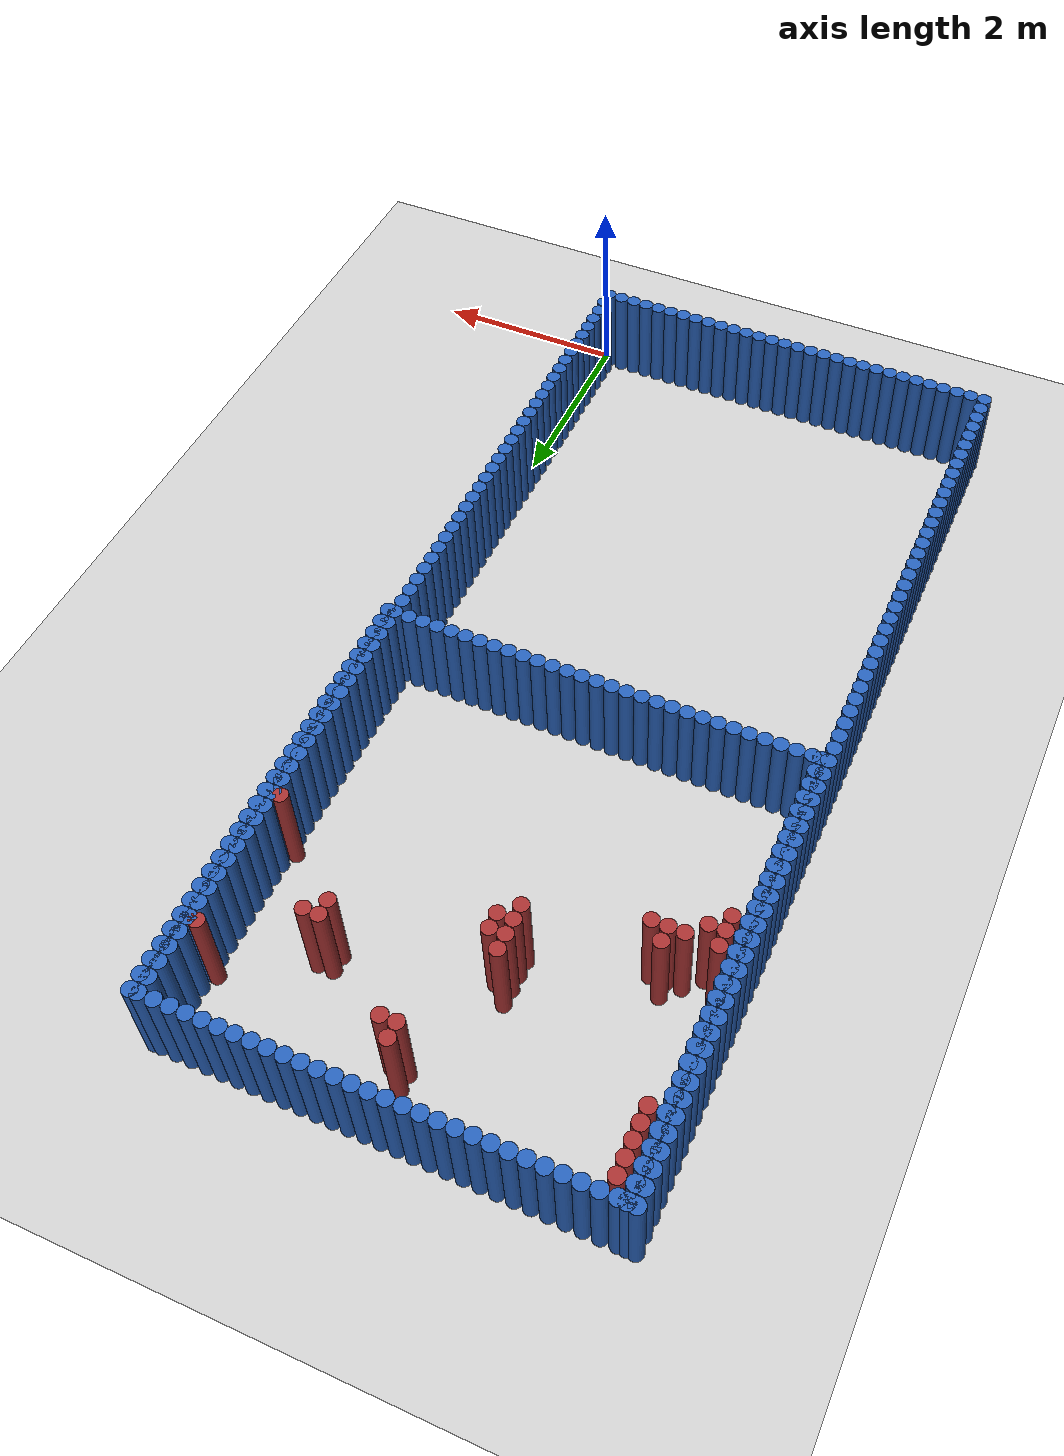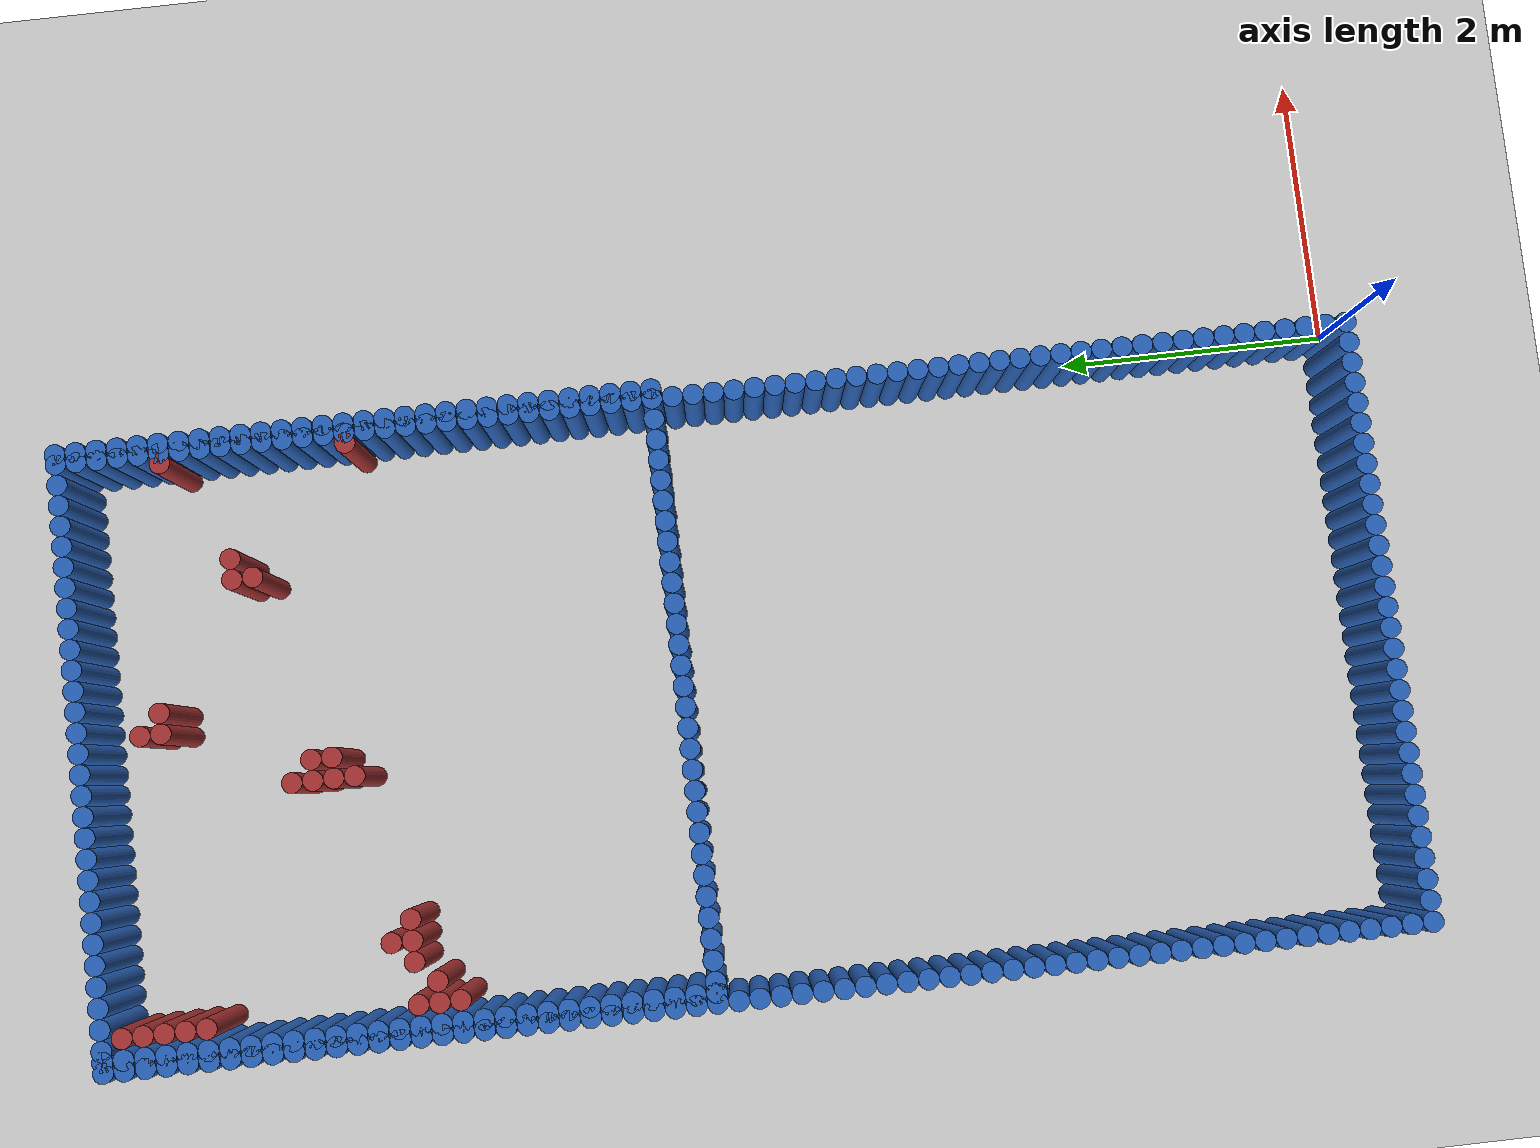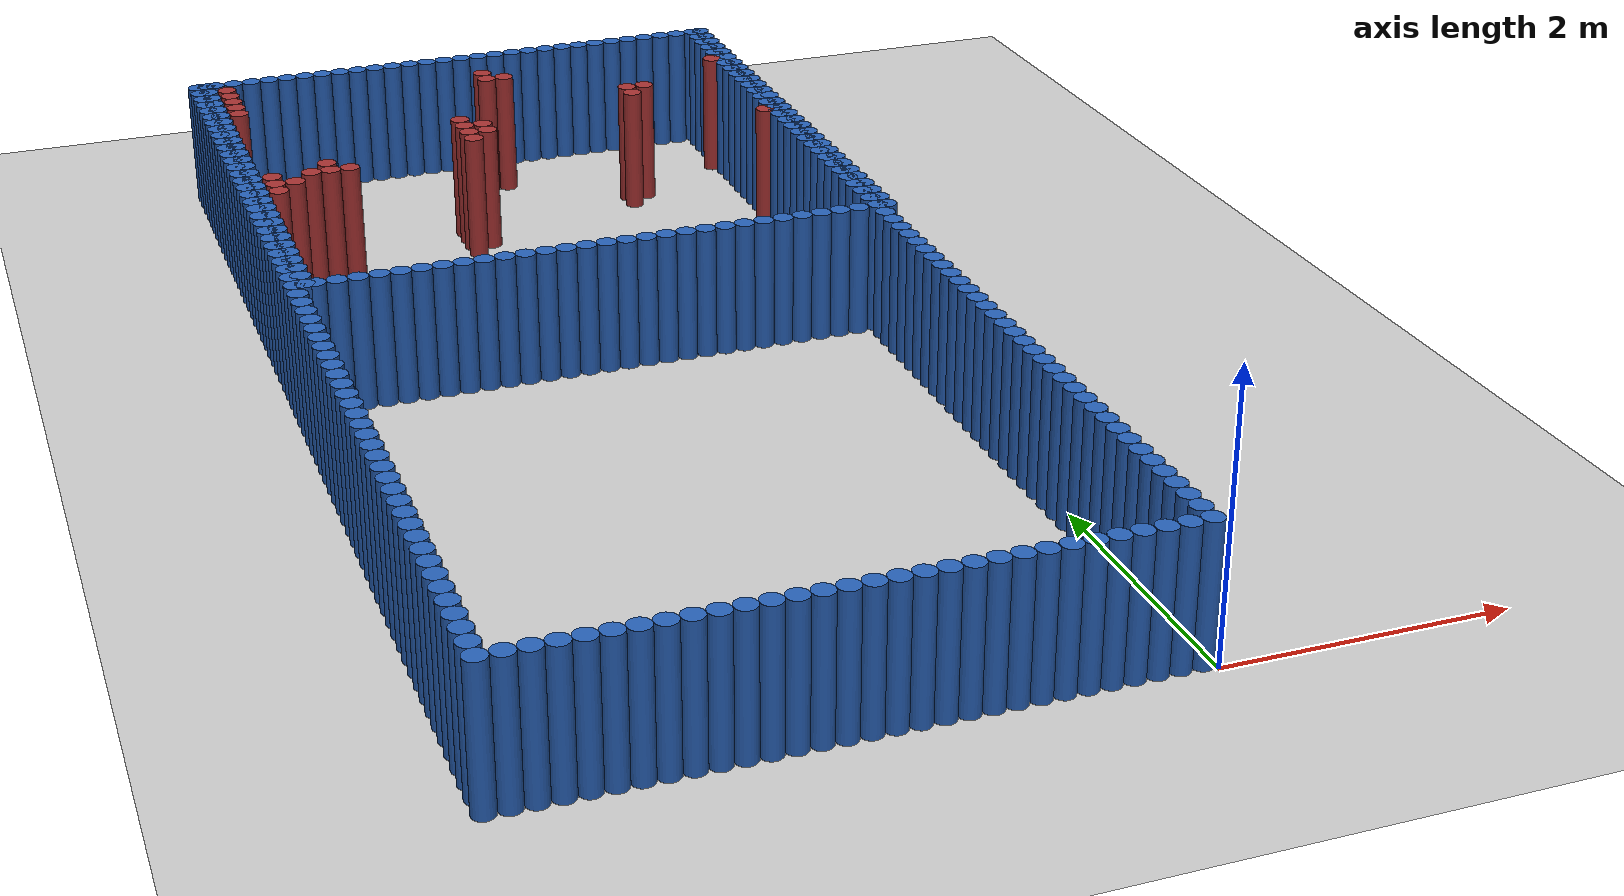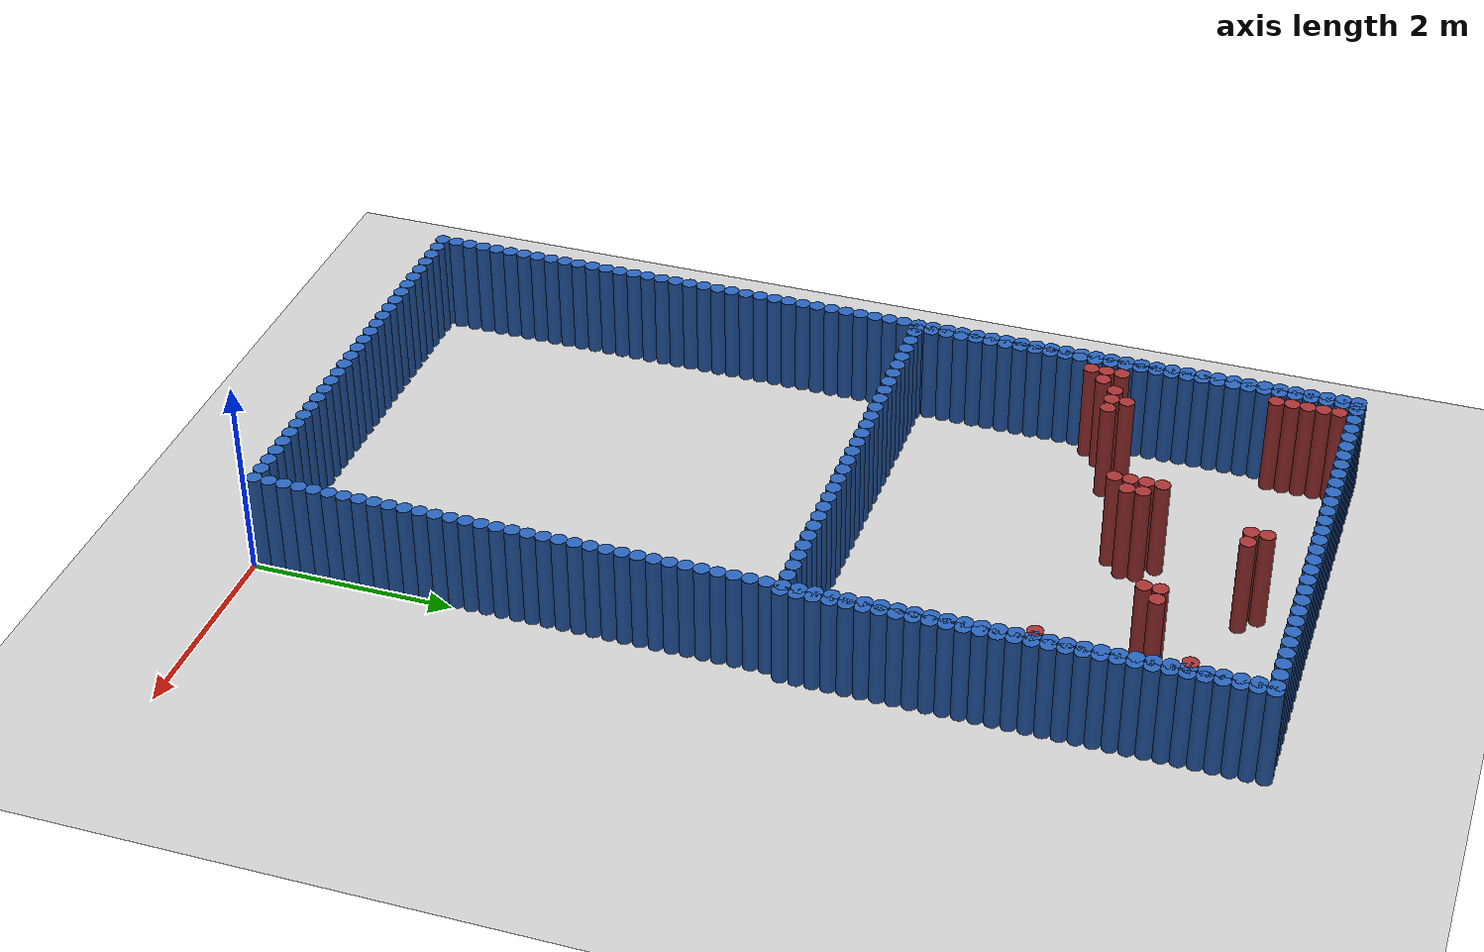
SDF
<?xml version="1.0" ?>
<sdf version='1.6'>
  <world name='barn_world'>
    <light name='sun' type='directional'>
      <cast_shadows>0</cast_shadows>
      <pose frame=''>0 0 10 0 -0 0</pose>
      <diffuse>0.8 0.8 0.8 1</diffuse>
      <specular>0.1 0.1 0.1 1</specular>
      <direction>-0.5 0.5 -1</direction>
    </light>
    <model name='ground_plane'>
      <static>1</static>
      <link name='link'>
        <collision name='collision'><geometry><plane><normal>0 0 1</normal><size>100 100</size></plane></geometry></collision>
        <visual name='visual'><geometry><plane><normal>0 0 1</normal><size>100 100</size></plane></geometry><material><script><uri>file://media/materials/scripts/gazebo.material</uri><name>Gazebo/Grey</name></script></material></visual>
      </link>
    </model>
    <gravity>0 0 -9.8</gravity>
    <physics name='default_physics' default='0' type='ode'>
      <max_step_size>0.01</max_step_size>
      <real_time_factor>1</real_time_factor>
      <real_time_update_rate>100</real_time_update_rate>
    </physics>

    <model name="unit_cylinder_0">
      <static>1</static>
      <pose frame="">-0.0750 0.0750 0.5 0 0 0</pose>
      <link name="link">
        <collision name="collision"><geometry><cylinder><radius>0.075</radius><length>1</length></cylinder></geometry></collision>
        <visual name="visual"><geometry><cylinder><radius>0.075</radius><length>1</length></cylinder></geometry><material><ambient>0.152 0.379 0.72 1</ambient><diffuse>0.152 0.379 0.72 1</diffuse></material></visual>
      </link>
    </model>

    <model name="unit_cylinder_1">
      <static>1</static>
      <pose frame="">-0.2250 0.0750 0.5 0 0 0</pose>
      <link name="link">
        <collision name="collision"><geometry><cylinder><radius>0.075</radius><length>1</length></cylinder></geometry></collision>
        <visual name="visual"><geometry><cylinder><radius>0.075</radius><length>1</length></cylinder></geometry><material><ambient>0.152 0.379 0.72 1</ambient><diffuse>0.152 0.379 0.72 1</diffuse></material></visual>
      </link>
    </model>

    <model name="unit_cylinder_2">
      <static>1</static>
      <pose frame="">-0.3750 0.0750 0.5 0 0 0</pose>
      <link name="link">
        <collision name="collision"><geometry><cylinder><radius>0.075</radius><length>1</length></cylinder></geometry></collision>
        <visual name="visual"><geometry><cylinder><radius>0.075</radius><length>1</length></cylinder></geometry><material><ambient>0.152 0.379 0.72 1</ambient><diffuse>0.152 0.379 0.72 1</diffuse></material></visual>
      </link>
    </model>

    <model name="unit_cylinder_3">
      <static>1</static>
      <pose frame="">-0.5250 0.0750 0.5 0 0 0</pose>
      <link name="link">
        <collision name="collision"><geometry><cylinder><radius>0.075</radius><length>1</length></cylinder></geometry></collision>
        <visual name="visual"><geometry><cylinder><radius>0.075</radius><length>1</length></cylinder></geometry><material><ambient>0.152 0.379 0.72 1</ambient><diffuse>0.152 0.379 0.72 1</diffuse></material></visual>
      </link>
    </model>

    <model name="unit_cylinder_4">
      <static>1</static>
      <pose frame="">-0.6750 0.0750 0.5 0 0 0</pose>
      <link name="link">
        <collision name="collision"><geometry><cylinder><radius>0.075</radius><length>1</length></cylinder></geometry></collision>
        <visual name="visual"><geometry><cylinder><radius>0.075</radius><length>1</length></cylinder></geometry><material><ambient>0.152 0.379 0.72 1</ambient><diffuse>0.152 0.379 0.72 1</diffuse></material></visual>
      </link>
    </model>

    <model name="unit_cylinder_5">
      <static>1</static>
      <pose frame="">-0.8250 0.0750 0.5 0 0 0</pose>
      <link name="link">
        <collision name="collision"><geometry><cylinder><radius>0.075</radius><length>1</length></cylinder></geometry></collision>
        <visual name="visual"><geometry><cylinder><radius>0.075</radius><length>1</length></cylinder></geometry><material><ambient>0.152 0.379 0.72 1</ambient><diffuse>0.152 0.379 0.72 1</diffuse></material></visual>
      </link>
    </model>

    <model name="unit_cylinder_6">
      <static>1</static>
      <pose frame="">-0.9750 0.0750 0.5 0 0 0</pose>
      <link name="link">
        <collision name="collision"><geometry><cylinder><radius>0.075</radius><length>1</length></cylinder></geometry></collision>
        <visual name="visual"><geometry><cylinder><radius>0.075</radius><length>1</length></cylinder></geometry><material><ambient>0.152 0.379 0.72 1</ambient><diffuse>0.152 0.379 0.72 1</diffuse></material></visual>
      </link>
    </model>

    <model name="unit_cylinder_7">
      <static>1</static>
      <pose frame="">-1.1250 0.0750 0.5 0 0 0</pose>
      <link name="link">
        <collision name="collision"><geometry><cylinder><radius>0.075</radius><length>1</length></cylinder></geometry></collision>
        <visual name="visual"><geometry><cylinder><radius>0.075</radius><length>1</length></cylinder></geometry><material><ambient>0.152 0.379 0.72 1</ambient><diffuse>0.152 0.379 0.72 1</diffuse></material></visual>
      </link>
    </model>

    <model name="unit_cylinder_8">
      <static>1</static>
      <pose frame="">-1.2750 0.0750 0.5 0 0 0</pose>
      <link name="link">
        <collision name="collision"><geometry><cylinder><radius>0.075</radius><length>1</length></cylinder></geometry></collision>
        <visual name="visual"><geometry><cylinder><radius>0.075</radius><length>1</length></cylinder></geometry><material><ambient>0.152 0.379 0.72 1</ambient><diffuse>0.152 0.379 0.72 1</diffuse></material></visual>
      </link>
    </model>

    <model name="unit_cylinder_9">
      <static>1</static>
      <pose frame="">-1.4250 0.0750 0.5 0 0 0</pose>
      <link name="link">
        <collision name="collision"><geometry><cylinder><radius>0.075</radius><length>1</length></cylinder></geometry></collision>
        <visual name="visual"><geometry><cylinder><radius>0.075</radius><length>1</length></cylinder></geometry><material><ambient>0.152 0.379 0.72 1</ambient><diffuse>0.152 0.379 0.72 1</diffuse></material></visual>
      </link>
    </model>

    <model name="unit_cylinder_10">
      <static>1</static>
      <pose frame="">-1.5750 0.0750 0.5 0 0 0</pose>
      <link name="link">
        <collision name="collision"><geometry><cylinder><radius>0.075</radius><length>1</length></cylinder></geometry></collision>
        <visual name="visual"><geometry><cylinder><radius>0.075</radius><length>1</length></cylinder></geometry><material><ambient>0.152 0.379 0.72 1</ambient><diffuse>0.152 0.379 0.72 1</diffuse></material></visual>
      </link>
    </model>

    <model name="unit_cylinder_11">
      <static>1</static>
      <pose frame="">-1.7250 0.0750 0.5 0 0 0</pose>
      <link name="link">
        <collision name="collision"><geometry><cylinder><radius>0.075</radius><length>1</length></cylinder></geometry></collision>
        <visual name="visual"><geometry><cylinder><radius>0.075</radius><length>1</length></cylinder></geometry><material><ambient>0.152 0.379 0.72 1</ambient><diffuse>0.152 0.379 0.72 1</diffuse></material></visual>
      </link>
    </model>

    <model name="unit_cylinder_12">
      <static>1</static>
      <pose frame="">-1.8750 0.0750 0.5 0 0 0</pose>
      <link name="link">
        <collision name="collision"><geometry><cylinder><radius>0.075</radius><length>1</length></cylinder></geometry></collision>
        <visual name="visual"><geometry><cylinder><radius>0.075</radius><length>1</length></cylinder></geometry><material><ambient>0.152 0.379 0.72 1</ambient><diffuse>0.152 0.379 0.72 1</diffuse></material></visual>
      </link>
    </model>

    <model name="unit_cylinder_13">
      <static>1</static>
      <pose frame="">-2.0250 0.0750 0.5 0 0 0</pose>
      <link name="link">
        <collision name="collision"><geometry><cylinder><radius>0.075</radius><length>1</length></cylinder></geometry></collision>
        <visual name="visual"><geometry><cylinder><radius>0.075</radius><length>1</length></cylinder></geometry><material><ambient>0.152 0.379 0.72 1</ambient><diffuse>0.152 0.379 0.72 1</diffuse></material></visual>
      </link>
    </model>

    <model name="unit_cylinder_14">
      <static>1</static>
      <pose frame="">-2.1750 0.0750 0.5 0 0 0</pose>
      <link name="link">
        <collision name="collision"><geometry><cylinder><radius>0.075</radius><length>1</length></cylinder></geometry></collision>
        <visual name="visual"><geometry><cylinder><radius>0.075</radius><length>1</length></cylinder></geometry><material><ambient>0.152 0.379 0.72 1</ambient><diffuse>0.152 0.379 0.72 1</diffuse></material></visual>
      </link>
    </model>

    <model name="unit_cylinder_15">
      <static>1</static>
      <pose frame="">-2.3250 0.0750 0.5 0 0 0</pose>
      <link name="link">
        <collision name="collision"><geometry><cylinder><radius>0.075</radius><length>1</length></cylinder></geometry></collision>
        <visual name="visual"><geometry><cylinder><radius>0.075</radius><length>1</length></cylinder></geometry><material><ambient>0.152 0.379 0.72 1</ambient><diffuse>0.152 0.379 0.72 1</diffuse></material></visual>
      </link>
    </model>

    <model name="unit_cylinder_16">
      <static>1</static>
      <pose frame="">-2.4750 0.0750 0.5 0 0 0</pose>
      <link name="link">
        <collision name="collision"><geometry><cylinder><radius>0.075</radius><length>1</length></cylinder></geometry></collision>
        <visual name="visual"><geometry><cylinder><radius>0.075</radius><length>1</length></cylinder></geometry><material><ambient>0.152 0.379 0.72 1</ambient><diffuse>0.152 0.379 0.72 1</diffuse></material></visual>
      </link>
    </model>

    <model name="unit_cylinder_17">
      <static>1</static>
      <pose frame="">-2.6250 0.0750 0.5 0 0 0</pose>
      <link name="link">
        <collision name="collision"><geometry><cylinder><radius>0.075</radius><length>1</length></cylinder></geometry></collision>
        <visual name="visual"><geometry><cylinder><radius>0.075</radius><length>1</length></cylinder></geometry><material><ambient>0.152 0.379 0.72 1</ambient><diffuse>0.152 0.379 0.72 1</diffuse></material></visual>
      </link>
    </model>

    <model name="unit_cylinder_18">
      <static>1</static>
      <pose frame="">-2.7750 0.0750 0.5 0 0 0</pose>
      <link name="link">
        <collision name="collision"><geometry><cylinder><radius>0.075</radius><length>1</length></cylinder></geometry></collision>
        <visual name="visual"><geometry><cylinder><radius>0.075</radius><length>1</length></cylinder></geometry><material><ambient>0.152 0.379 0.72 1</ambient><diffuse>0.152 0.379 0.72 1</diffuse></material></visual>
      </link>
    </model>

    <model name="unit_cylinder_19">
      <static>1</static>
      <pose frame="">-2.9250 0.0750 0.5 0 0 0</pose>
      <link name="link">
        <collision name="collision"><geometry><cylinder><radius>0.075</radius><length>1</length></cylinder></geometry></collision>
        <visual name="visual"><geometry><cylinder><radius>0.075</radius><length>1</length></cylinder></geometry><material><ambient>0.152 0.379 0.72 1</ambient><diffuse>0.152 0.379 0.72 1</diffuse></material></visual>
      </link>
    </model>

    <model name="unit_cylinder_20">
      <static>1</static>
      <pose frame="">-3.0750 0.0750 0.5 0 0 0</pose>
      <link name="link">
        <collision name="collision"><geometry><cylinder><radius>0.075</radius><length>1</length></cylinder></geometry></collision>
        <visual name="visual"><geometry><cylinder><radius>0.075</radius><length>1</length></cylinder></geometry><material><ambient>0.152 0.379 0.72 1</ambient><diffuse>0.152 0.379 0.72 1</diffuse></material></visual>
      </link>
    </model>

    <model name="unit_cylinder_21">
      <static>1</static>
      <pose frame="">-3.2250 0.0750 0.5 0 0 0</pose>
      <link name="link">
        <collision name="collision"><geometry><cylinder><radius>0.075</radius><length>1</length></cylinder></geometry></collision>
        <visual name="visual"><geometry><cylinder><radius>0.075</radius><length>1</length></cylinder></geometry><material><ambient>0.152 0.379 0.72 1</ambient><diffuse>0.152 0.379 0.72 1</diffuse></material></visual>
      </link>
    </model>

    <model name="unit_cylinder_22">
      <static>1</static>
      <pose frame="">-3.3750 0.0750 0.5 0 0 0</pose>
      <link name="link">
        <collision name="collision"><geometry><cylinder><radius>0.075</radius><length>1</length></cylinder></geometry></collision>
        <visual name="visual"><geometry><cylinder><radius>0.075</radius><length>1</length></cylinder></geometry><material><ambient>0.152 0.379 0.72 1</ambient><diffuse>0.152 0.379 0.72 1</diffuse></material></visual>
      </link>
    </model>

    <model name="unit_cylinder_23">
      <static>1</static>
      <pose frame="">-3.5250 0.0750 0.5 0 0 0</pose>
      <link name="link">
        <collision name="collision"><geometry><cylinder><radius>0.075</radius><length>1</length></cylinder></geometry></collision>
        <visual name="visual"><geometry><cylinder><radius>0.075</radius><length>1</length></cylinder></geometry><material><ambient>0.152 0.379 0.72 1</ambient><diffuse>0.152 0.379 0.72 1</diffuse></material></visual>
      </link>
    </model>

    <model name="unit_cylinder_24">
      <static>1</static>
      <pose frame="">-3.6750 0.0750 0.5 0 0 0</pose>
      <link name="link">
        <collision name="collision"><geometry><cylinder><radius>0.075</radius><length>1</length></cylinder></geometry></collision>
        <visual name="visual"><geometry><cylinder><radius>0.075</radius><length>1</length></cylinder></geometry><material><ambient>0.152 0.379 0.72 1</ambient><diffuse>0.152 0.379 0.72 1</diffuse></material></visual>
      </link>
    </model>

    <model name="unit_cylinder_25">
      <static>1</static>
      <pose frame="">-3.8250 0.0750 0.5 0 0 0</pose>
      <link name="link">
        <collision name="collision"><geometry><cylinder><radius>0.075</radius><length>1</length></cylinder></geometry></collision>
        <visual name="visual"><geometry><cylinder><radius>0.075</radius><length>1</length></cylinder></geometry><material><ambient>0.152 0.379 0.72 1</ambient><diffuse>0.152 0.379 0.72 1</diffuse></material></visual>
      </link>
    </model>

    <model name="unit_cylinder_26">
      <static>1</static>
      <pose frame="">-3.9750 0.0750 0.5 0 0 0</pose>
      <link name="link">
        <collision name="collision"><geometry><cylinder><radius>0.075</radius><length>1</length></cylinder></geometry></collision>
        <visual name="visual"><geometry><cylinder><radius>0.075</radius><length>1</length></cylinder></geometry><material><ambient>0.152 0.379 0.72 1</ambient><diffuse>0.152 0.379 0.72 1</diffuse></material></visual>
      </link>
    </model>

    <model name="unit_cylinder_27">
      <static>1</static>
      <pose frame="">-4.1250 0.0750 0.5 0 0 0</pose>
      <link name="link">
        <collision name="collision"><geometry><cylinder><radius>0.075</radius><length>1</length></cylinder></geometry></collision>
        <visual name="visual"><geometry><cylinder><radius>0.075</radius><length>1</length></cylinder></geometry><material><ambient>0.152 0.379 0.72 1</ambient><diffuse>0.152 0.379 0.72 1</diffuse></material></visual>
      </link>
    </model>

    <model name="unit_cylinder_28">
      <static>1</static>
      <pose frame="">-4.2750 0.0750 0.5 0 0 0</pose>
      <link name="link">
        <collision name="collision"><geometry><cylinder><radius>0.075</radius><length>1</length></cylinder></geometry></collision>
        <visual name="visual"><geometry><cylinder><radius>0.075</radius><length>1</length></cylinder></geometry><material><ambient>0.152 0.379 0.72 1</ambient><diffuse>0.152 0.379 0.72 1</diffuse></material></visual>
      </link>
    </model>

    <model name="unit_cylinder_29">
      <static>1</static>
      <pose frame="">-4.4250 0.0750 0.5 0 0 0</pose>
      <link name="link">
        <collision name="collision"><geometry><cylinder><radius>0.075</radius><length>1</length></cylinder></geometry></collision>
        <visual name="visual"><geometry><cylinder><radius>0.075</radius><length>1</length></cylinder></geometry><material><ambient>0.152 0.379 0.72 1</ambient><diffuse>0.152 0.379 0.72 1</diffuse></material></visual>
      </link>
    </model>

    <model name="unit_cylinder_30">
      <static>1</static>
      <pose frame="">-0.0750 0.2250 0.5 0 0 0</pose>
      <link name="link">
        <collision name="collision"><geometry><cylinder><radius>0.075</radius><length>1</length></cylinder></geometry></collision>
        <visual name="visual"><geometry><cylinder><radius>0.075</radius><length>1</length></cylinder></geometry><material><ambient>0.152 0.379 0.72 1</ambient><diffuse>0.152 0.379 0.72 1</diffuse></material></visual>
      </link>
    </model>

    <model name="unit_cylinder_31">
      <static>1</static>
      <pose frame="">-4.4250 0.2250 0.5 0 0 0</pose>
      <link name="link">
        <collision name="collision"><geometry><cylinder><radius>0.075</radius><length>1</length></cylinder></geometry></collision>
        <visual name="visual"><geometry><cylinder><radius>0.075</radius><length>1</length></cylinder></geometry><material><ambient>0.152 0.379 0.72 1</ambient><diffuse>0.152 0.379 0.72 1</diffuse></material></visual>
      </link>
    </model>

    <model name="unit_cylinder_32">
      <static>1</static>
      <pose frame="">-0.0750 0.3750 0.5 0 0 0</pose>
      <link name="link">
        <collision name="collision"><geometry><cylinder><radius>0.075</radius><length>1</length></cylinder></geometry></collision>
        <visual name="visual"><geometry><cylinder><radius>0.075</radius><length>1</length></cylinder></geometry><material><ambient>0.152 0.379 0.72 1</ambient><diffuse>0.152 0.379 0.72 1</diffuse></material></visual>
      </link>
    </model>

    <model name="unit_cylinder_33">
      <static>1</static>
      <pose frame="">-4.4250 0.3750 0.5 0 0 0</pose>
      <link name="link">
        <collision name="collision"><geometry><cylinder><radius>0.075</radius><length>1</length></cylinder></geometry></collision>
        <visual name="visual"><geometry><cylinder><radius>0.075</radius><length>1</length></cylinder></geometry><material><ambient>0.152 0.379 0.72 1</ambient><diffuse>0.152 0.379 0.72 1</diffuse></material></visual>
      </link>
    </model>

    <model name="unit_cylinder_34">
      <static>1</static>
      <pose frame="">-0.0750 0.5250 0.5 0 0 0</pose>
      <link name="link">
        <collision name="collision"><geometry><cylinder><radius>0.075</radius><length>1</length></cylinder></geometry></collision>
        <visual name="visual"><geometry><cylinder><radius>0.075</radius><length>1</length></cylinder></geometry><material><ambient>0.152 0.379 0.72 1</ambient><diffuse>0.152 0.379 0.72 1</diffuse></material></visual>
      </link>
    </model>

    <model name="unit_cylinder_35">
      <static>1</static>
      <pose frame="">-4.4250 0.5250 0.5 0 0 0</pose>
      <link name="link">
        <collision name="collision"><geometry><cylinder><radius>0.075</radius><length>1</length></cylinder></geometry></collision>
        <visual name="visual"><geometry><cylinder><radius>0.075</radius><length>1</length></cylinder></geometry><material><ambient>0.152 0.379 0.72 1</ambient><diffuse>0.152 0.379 0.72 1</diffuse></material></visual>
      </link>
    </model>

    <model name="unit_cylinder_36">
      <static>1</static>
      <pose frame="">-0.0750 0.6750 0.5 0 0 0</pose>
      <link name="link">
        <collision name="collision"><geometry><cylinder><radius>0.075</radius><length>1</length></cylinder></geometry></collision>
        <visual name="visual"><geometry><cylinder><radius>0.075</radius><length>1</length></cylinder></geometry><material><ambient>0.152 0.379 0.72 1</ambient><diffuse>0.152 0.379 0.72 1</diffuse></material></visual>
      </link>
    </model>

    <model name="unit_cylinder_37">
      <static>1</static>
      <pose frame="">-4.4250 0.6750 0.5 0 0 0</pose>
      <link name="link">
        <collision name="collision"><geometry><cylinder><radius>0.075</radius><length>1</length></cylinder></geometry></collision>
        <visual name="visual"><geometry><cylinder><radius>0.075</radius><length>1</length></cylinder></geometry><material><ambient>0.152 0.379 0.72 1</ambient><diffuse>0.152 0.379 0.72 1</diffuse></material></visual>
      </link>
    </model>

    <model name="unit_cylinder_38">
      <static>1</static>
      <pose frame="">-0.0750 0.8250 0.5 0 0 0</pose>
      <link name="link">
        <collision name="collision"><geometry><cylinder><radius>0.075</radius><length>1</length></cylinder></geometry></collision>
        <visual name="visual"><geometry><cylinder><radius>0.075</radius><length>1</length></cylinder></geometry><material><ambient>0.152 0.379 0.72 1</ambient><diffuse>0.152 0.379 0.72 1</diffuse></material></visual>
      </link>
    </model>

    <model name="unit_cylinder_39">
      <static>1</static>
      <pose frame="">-4.4250 0.8250 0.5 0 0 0</pose>
      <link name="link">
        <collision name="collision"><geometry><cylinder><radius>0.075</radius><length>1</length></cylinder></geometry></collision>
        <visual name="visual"><geometry><cylinder><radius>0.075</radius><length>1</length></cylinder></geometry><material><ambient>0.152 0.379 0.72 1</ambient><diffuse>0.152 0.379 0.72 1</diffuse></material></visual>
      </link>
    </model>

    <model name="unit_cylinder_40">
      <static>1</static>
      <pose frame="">-0.0750 0.9750 0.5 0 0 0</pose>
      <link name="link">
        <collision name="collision"><geometry><cylinder><radius>0.075</radius><length>1</length></cylinder></geometry></collision>
        <visual name="visual"><geometry><cylinder><radius>0.075</radius><length>1</length></cylinder></geometry><material><ambient>0.152 0.379 0.72 1</ambient><diffuse>0.152 0.379 0.72 1</diffuse></material></visual>
      </link>
    </model>

    <model name="unit_cylinder_41">
      <static>1</static>
      <pose frame="">-4.4250 0.9750 0.5 0 0 0</pose>
      <link name="link">
        <collision name="collision"><geometry><cylinder><radius>0.075</radius><length>1</length></cylinder></geometry></collision>
        <visual name="visual"><geometry><cylinder><radius>0.075</radius><length>1</length></cylinder></geometry><material><ambient>0.152 0.379 0.72 1</ambient><diffuse>0.152 0.379 0.72 1</diffuse></material></visual>
      </link>
    </model>

    <model name="unit_cylinder_42">
      <static>1</static>
      <pose frame="">-0.0750 1.1250 0.5 0 0 0</pose>
      <link name="link">
        <collision name="collision"><geometry><cylinder><radius>0.075</radius><length>1</length></cylinder></geometry></collision>
        <visual name="visual"><geometry><cylinder><radius>0.075</radius><length>1</length></cylinder></geometry><material><ambient>0.152 0.379 0.72 1</ambient><diffuse>0.152 0.379 0.72 1</diffuse></material></visual>
      </link>
    </model>

    <model name="unit_cylinder_43">
      <static>1</static>
      <pose frame="">-4.4250 1.1250 0.5 0 0 0</pose>
      <link name="link">
        <collision name="collision"><geometry><cylinder><radius>0.075</radius><length>1</length></cylinder></geometry></collision>
        <visual name="visual"><geometry><cylinder><radius>0.075</radius><length>1</length></cylinder></geometry><material><ambient>0.152 0.379 0.72 1</ambient><diffuse>0.152 0.379 0.72 1</diffuse></material></visual>
      </link>
    </model>

    <model name="unit_cylinder_44">
      <static>1</static>
      <pose frame="">-0.0750 1.2750 0.5 0 0 0</pose>
      <link name="link">
        <collision name="collision"><geometry><cylinder><radius>0.075</radius><length>1</length></cylinder></geometry></collision>
        <visual name="visual"><geometry><cylinder><radius>0.075</radius><length>1</length></cylinder></geometry><material><ambient>0.152 0.379 0.72 1</ambient><diffuse>0.152 0.379 0.72 1</diffuse></material></visual>
      </link>
    </model>

    <model name="unit_cylinder_45">
      <static>1</static>
      <pose frame="">-4.4250 1.2750 0.5 0 0 0</pose>
      <link name="link">
        <collision name="collision"><geometry><cylinder><radius>0.075</radius><length>1</length></cylinder></geometry></collision>
        <visual name="visual"><geometry><cylinder><radius>0.075</radius><length>1</length></cylinder></geometry><material><ambient>0.152 0.379 0.72 1</ambient><diffuse>0.152 0.379 0.72 1</diffuse></material></visual>
      </link>
    </model>

    <model name="unit_cylinder_46">
      <static>1</static>
      <pose frame="">-0.0750 1.4250 0.5 0 0 0</pose>
      <link name="link">
        <collision name="collision"><geometry><cylinder><radius>0.075</radius><length>1</length></cylinder></geometry></collision>
        <visual name="visual"><geometry><cylinder><radius>0.075</radius><length>1</length></cylinder></geometry><material><ambient>0.152 0.379 0.72 1</ambient><diffuse>0.152 0.379 0.72 1</diffuse></material></visual>
      </link>
    </model>

    <model name="unit_cylinder_47">
      <static>1</static>
      <pose frame="">-4.4250 1.4250 0.5 0 0 0</pose>
      <link name="link">
        <collision name="collision"><geometry><cylinder><radius>0.075</radius><length>1</length></cylinder></geometry></collision>
        <visual name="visual"><geometry><cylinder><radius>0.075</radius><length>1</length></cylinder></geometry><material><ambient>0.152 0.379 0.72 1</ambient><diffuse>0.152 0.379 0.72 1</diffuse></material></visual>
      </link>
    </model>

    <model name="unit_cylinder_48">
      <static>1</static>
      <pose frame="">-0.0750 1.5750 0.5 0 0 0</pose>
      <link name="link">
        <collision name="collision"><geometry><cylinder><radius>0.075</radius><length>1</length></cylinder></geometry></collision>
        <visual name="visual"><geometry><cylinder><radius>0.075</radius><length>1</length></cylinder></geometry><material><ambient>0.152 0.379 0.72 1</ambient><diffuse>0.152 0.379 0.72 1</diffuse></material></visual>
      </link>
    </model>

    <model name="unit_cylinder_49">
      <static>1</static>
      <pose frame="">-4.4250 1.5750 0.5 0 0 0</pose>
      <link name="link">
        <collision name="collision"><geometry><cylinder><radius>0.075</radius><length>1</length></cylinder></geometry></collision>
        <visual name="visual"><geometry><cylinder><radius>0.075</radius><length>1</length></cylinder></geometry><material><ambient>0.152 0.379 0.72 1</ambient><diffuse>0.152 0.379 0.72 1</diffuse></material></visual>
      </link>
    </model>

    <model name="unit_cylinder_50">
      <static>1</static>
      <pose frame="">-0.0750 1.7250 0.5 0 0 0</pose>
      <link name="link">
        <collision name="collision"><geometry><cylinder><radius>0.075</radius><length>1</length></cylinder></geometry></collision>
        <visual name="visual"><geometry><cylinder><radius>0.075</radius><length>1</length></cylinder></geometry><material><ambient>0.152 0.379 0.72 1</ambient><diffuse>0.152 0.379 0.72 1</diffuse></material></visual>
      </link>
    </model>

    <model name="unit_cylinder_51">
      <static>1</static>
      <pose frame="">-4.4250 1.7250 0.5 0 0 0</pose>
      <link name="link">
        <collision name="collision"><geometry><cylinder><radius>0.075</radius><length>1</length></cylinder></geometry></collision>
        <visual name="visual"><geometry><cylinder><radius>0.075</radius><length>1</length></cylinder></geometry><material><ambient>0.152 0.379 0.72 1</ambient><diffuse>0.152 0.379 0.72 1</diffuse></material></visual>
      </link>
    </model>

    <model name="unit_cylinder_52">
      <static>1</static>
      <pose frame="">-0.0750 1.8750 0.5 0 0 0</pose>
      <link name="link">
        <collision name="collision"><geometry><cylinder><radius>0.075</radius><length>1</length></cylinder></geometry></collision>
        <visual name="visual"><geometry><cylinder><radius>0.075</radius><length>1</length></cylinder></geometry><material><ambient>0.152 0.379 0.72 1</ambient><diffuse>0.152 0.379 0.72 1</diffuse></material></visual>
      </link>
    </model>

    <model name="unit_cylinder_53">
      <static>1</static>
      <pose frame="">-4.4250 1.8750 0.5 0 0 0</pose>
      <link name="link">
        <collision name="collision"><geometry><cylinder><radius>0.075</radius><length>1</length></cylinder></geometry></collision>
        <visual name="visual"><geometry><cylinder><radius>0.075</radius><length>1</length></cylinder></geometry><material><ambient>0.152 0.379 0.72 1</ambient><diffuse>0.152 0.379 0.72 1</diffuse></material></visual>
      </link>
    </model>

    <model name="unit_cylinder_54">
      <static>1</static>
      <pose frame="">-0.0750 2.0250 0.5 0 0 0</pose>
      <link name="link">
        <collision name="collision"><geometry><cylinder><radius>0.075</radius><length>1</length></cylinder></geometry></collision>
        <visual name="visual"><geometry><cylinder><radius>0.075</radius><length>1</length></cylinder></geometry><material><ambient>0.152 0.379 0.72 1</ambient><diffuse>0.152 0.379 0.72 1</diffuse></material></visual>
      </link>
    </model>

    <model name="unit_cylinder_55">
      <static>1</static>
      <pose frame="">-4.4250 2.0250 0.5 0 0 0</pose>
      <link name="link">
        <collision name="collision"><geometry><cylinder><radius>0.075</radius><length>1</length></cylinder></geometry></collision>
        <visual name="visual"><geometry><cylinder><radius>0.075</radius><length>1</length></cylinder></geometry><material><ambient>0.152 0.379 0.72 1</ambient><diffuse>0.152 0.379 0.72 1</diffuse></material></visual>
      </link>
    </model>

    <model name="unit_cylinder_56">
      <static>1</static>
      <pose frame="">-0.0750 2.1750 0.5 0 0 0</pose>
      <link name="link">
        <collision name="collision"><geometry><cylinder><radius>0.075</radius><length>1</length></cylinder></geometry></collision>
        <visual name="visual"><geometry><cylinder><radius>0.075</radius><length>1</length></cylinder></geometry><material><ambient>0.152 0.379 0.72 1</ambient><diffuse>0.152 0.379 0.72 1</diffuse></material></visual>
      </link>
    </model>

    <model name="unit_cylinder_57">
      <static>1</static>
      <pose frame="">-4.4250 2.1750 0.5 0 0 0</pose>
      <link name="link">
        <collision name="collision"><geometry><cylinder><radius>0.075</radius><length>1</length></cylinder></geometry></collision>
        <visual name="visual"><geometry><cylinder><radius>0.075</radius><length>1</length></cylinder></geometry><material><ambient>0.152 0.379 0.72 1</ambient><diffuse>0.152 0.379 0.72 1</diffuse></material></visual>
      </link>
    </model>

    <model name="unit_cylinder_58">
      <static>1</static>
      <pose frame="">-0.0750 2.3250 0.5 0 0 0</pose>
      <link name="link">
        <collision name="collision"><geometry><cylinder><radius>0.075</radius><length>1</length></cylinder></geometry></collision>
        <visual name="visual"><geometry><cylinder><radius>0.075</radius><length>1</length></cylinder></geometry><material><ambient>0.152 0.379 0.72 1</ambient><diffuse>0.152 0.379 0.72 1</diffuse></material></visual>
      </link>
    </model>

    <model name="unit_cylinder_59">
      <static>1</static>
      <pose frame="">-4.4250 2.3250 0.5 0 0 0</pose>
      <link name="link">
        <collision name="collision"><geometry><cylinder><radius>0.075</radius><length>1</length></cylinder></geometry></collision>
        <visual name="visual"><geometry><cylinder><radius>0.075</radius><length>1</length></cylinder></geometry><material><ambient>0.152 0.379 0.72 1</ambient><diffuse>0.152 0.379 0.72 1</diffuse></material></visual>
      </link>
    </model>

    <model name="unit_cylinder_60">
      <static>1</static>
      <pose frame="">-0.0750 2.4750 0.5 0 0 0</pose>
      <link name="link">
        <collision name="collision"><geometry><cylinder><radius>0.075</radius><length>1</length></cylinder></geometry></collision>
        <visual name="visual"><geometry><cylinder><radius>0.075</radius><length>1</length></cylinder></geometry><material><ambient>0.152 0.379 0.72 1</ambient><diffuse>0.152 0.379 0.72 1</diffuse></material></visual>
      </link>
    </model>

    <model name="unit_cylinder_61">
      <static>1</static>
      <pose frame="">-4.4250 2.4750 0.5 0 0 0</pose>
      <link name="link">
        <collision name="collision"><geometry><cylinder><radius>0.075</radius><length>1</length></cylinder></geometry></collision>
        <visual name="visual"><geometry><cylinder><radius>0.075</radius><length>1</length></cylinder></geometry><material><ambient>0.152 0.379 0.72 1</ambient><diffuse>0.152 0.379 0.72 1</diffuse></material></visual>
      </link>
    </model>

    <model name="unit_cylinder_62">
      <static>1</static>
      <pose frame="">-0.0750 2.6250 0.5 0 0 0</pose>
      <link name="link">
        <collision name="collision"><geometry><cylinder><radius>0.075</radius><length>1</length></cylinder></geometry></collision>
        <visual name="visual"><geometry><cylinder><radius>0.075</radius><length>1</length></cylinder></geometry><material><ambient>0.152 0.379 0.72 1</ambient><diffuse>0.152 0.379 0.72 1</diffuse></material></visual>
      </link>
    </model>

    <model name="unit_cylinder_63">
      <static>1</static>
      <pose frame="">-4.4250 2.6250 0.5 0 0 0</pose>
      <link name="link">
        <collision name="collision"><geometry><cylinder><radius>0.075</radius><length>1</length></cylinder></geometry></collision>
        <visual name="visual"><geometry><cylinder><radius>0.075</radius><length>1</length></cylinder></geometry><material><ambient>0.152 0.379 0.72 1</ambient><diffuse>0.152 0.379 0.72 1</diffuse></material></visual>
      </link>
    </model>

    <model name="unit_cylinder_64">
      <static>1</static>
      <pose frame="">-0.0750 2.7750 0.5 0 0 0</pose>
      <link name="link">
        <collision name="collision"><geometry><cylinder><radius>0.075</radius><length>1</length></cylinder></geometry></collision>
        <visual name="visual"><geometry><cylinder><radius>0.075</radius><length>1</length></cylinder></geometry><material><ambient>0.152 0.379 0.72 1</ambient><diffuse>0.152 0.379 0.72 1</diffuse></material></visual>
      </link>
    </model>

    <model name="unit_cylinder_65">
      <static>1</static>
      <pose frame="">-4.4250 2.7750 0.5 0 0 0</pose>
      <link name="link">
        <collision name="collision"><geometry><cylinder><radius>0.075</radius><length>1</length></cylinder></geometry></collision>
        <visual name="visual"><geometry><cylinder><radius>0.075</radius><length>1</length></cylinder></geometry><material><ambient>0.152 0.379 0.72 1</ambient><diffuse>0.152 0.379 0.72 1</diffuse></material></visual>
      </link>
    </model>

    <model name="unit_cylinder_66">
      <static>1</static>
      <pose frame="">-0.0750 2.9250 0.5 0 0 0</pose>
      <link name="link">
        <collision name="collision"><geometry><cylinder><radius>0.075</radius><length>1</length></cylinder></geometry></collision>
        <visual name="visual"><geometry><cylinder><radius>0.075</radius><length>1</length></cylinder></geometry><material><ambient>0.152 0.379 0.72 1</ambient><diffuse>0.152 0.379 0.72 1</diffuse></material></visual>
      </link>
    </model>

    <model name="unit_cylinder_67">
      <static>1</static>
      <pose frame="">-4.4250 2.9250 0.5 0 0 0</pose>
      <link name="link">
        <collision name="collision"><geometry><cylinder><radius>0.075</radius><length>1</length></cylinder></geometry></collision>
        <visual name="visual"><geometry><cylinder><radius>0.075</radius><length>1</length></cylinder></geometry><material><ambient>0.152 0.379 0.72 1</ambient><diffuse>0.152 0.379 0.72 1</diffuse></material></visual>
      </link>
    </model>

    <model name="unit_cylinder_68">
      <static>1</static>
      <pose frame="">-0.0750 3.0750 0.5 0 0 0</pose>
      <link name="link">
        <collision name="collision"><geometry><cylinder><radius>0.075</radius><length>1</length></cylinder></geometry></collision>
        <visual name="visual"><geometry><cylinder><radius>0.075</radius><length>1</length></cylinder></geometry><material><ambient>0.152 0.379 0.72 1</ambient><diffuse>0.152 0.379 0.72 1</diffuse></material></visual>
      </link>
    </model>

    <model name="unit_cylinder_69">
      <static>1</static>
      <pose frame="">-4.4250 3.0750 0.5 0 0 0</pose>
      <link name="link">
        <collision name="collision"><geometry><cylinder><radius>0.075</radius><length>1</length></cylinder></geometry></collision>
        <visual name="visual"><geometry><cylinder><radius>0.075</radius><length>1</length></cylinder></geometry><material><ambient>0.152 0.379 0.72 1</ambient><diffuse>0.152 0.379 0.72 1</diffuse></material></visual>
      </link>
    </model>

    <model name="unit_cylinder_70">
      <static>1</static>
      <pose frame="">-0.0750 3.2250 0.5 0 0 0</pose>
      <link name="link">
        <collision name="collision"><geometry><cylinder><radius>0.075</radius><length>1</length></cylinder></geometry></collision>
        <visual name="visual"><geometry><cylinder><radius>0.075</radius><length>1</length></cylinder></geometry><material><ambient>0.152 0.379 0.72 1</ambient><diffuse>0.152 0.379 0.72 1</diffuse></material></visual>
      </link>
    </model>

    <model name="unit_cylinder_71">
      <static>1</static>
      <pose frame="">-4.4250 3.2250 0.5 0 0 0</pose>
      <link name="link">
        <collision name="collision"><geometry><cylinder><radius>0.075</radius><length>1</length></cylinder></geometry></collision>
        <visual name="visual"><geometry><cylinder><radius>0.075</radius><length>1</length></cylinder></geometry><material><ambient>0.152 0.379 0.72 1</ambient><diffuse>0.152 0.379 0.72 1</diffuse></material></visual>
      </link>
    </model>

    <model name="unit_cylinder_72">
      <static>1</static>
      <pose frame="">-0.0750 3.3750 0.5 0 0 0</pose>
      <link name="link">
        <collision name="collision"><geometry><cylinder><radius>0.075</radius><length>1</length></cylinder></geometry></collision>
        <visual name="visual"><geometry><cylinder><radius>0.075</radius><length>1</length></cylinder></geometry><material><ambient>0.152 0.379 0.72 1</ambient><diffuse>0.152 0.379 0.72 1</diffuse></material></visual>
      </link>
    </model>

    <model name="unit_cylinder_73">
      <static>1</static>
      <pose frame="">-4.4250 3.3750 0.5 0 0 0</pose>
      <link name="link">
        <collision name="collision"><geometry><cylinder><radius>0.075</radius><length>1</length></cylinder></geometry></collision>
        <visual name="visual"><geometry><cylinder><radius>0.075</radius><length>1</length></cylinder></geometry><material><ambient>0.152 0.379 0.72 1</ambient><diffuse>0.152 0.379 0.72 1</diffuse></material></visual>
      </link>
    </model>

    <model name="unit_cylinder_74">
      <static>1</static>
      <pose frame="">-0.0750 3.5250 0.5 0 0 0</pose>
      <link name="link">
        <collision name="collision"><geometry><cylinder><radius>0.075</radius><length>1</length></cylinder></geometry></collision>
        <visual name="visual"><geometry><cylinder><radius>0.075</radius><length>1</length></cylinder></geometry><material><ambient>0.152 0.379 0.72 1</ambient><diffuse>0.152 0.379 0.72 1</diffuse></material></visual>
      </link>
    </model>

    <model name="unit_cylinder_75">
      <static>1</static>
      <pose frame="">-4.4250 3.5250 0.5 0 0 0</pose>
      <link name="link">
        <collision name="collision"><geometry><cylinder><radius>0.075</radius><length>1</length></cylinder></geometry></collision>
        <visual name="visual"><geometry><cylinder><radius>0.075</radius><length>1</length></cylinder></geometry><material><ambient>0.152 0.379 0.72 1</ambient><diffuse>0.152 0.379 0.72 1</diffuse></material></visual>
      </link>
    </model>

    <model name="unit_cylinder_76">
      <static>1</static>
      <pose frame="">-0.0750 3.6750 0.5 0 0 0</pose>
      <link name="link">
        <collision name="collision"><geometry><cylinder><radius>0.075</radius><length>1</length></cylinder></geometry></collision>
        <visual name="visual"><geometry><cylinder><radius>0.075</radius><length>1</length></cylinder></geometry><material><ambient>0.152 0.379 0.72 1</ambient><diffuse>0.152 0.379 0.72 1</diffuse></material></visual>
      </link>
    </model>

    <model name="unit_cylinder_77">
      <static>1</static>
      <pose frame="">-4.4250 3.6750 0.5 0 0 0</pose>
      <link name="link">
        <collision name="collision"><geometry><cylinder><radius>0.075</radius><length>1</length></cylinder></geometry></collision>
        <visual name="visual"><geometry><cylinder><radius>0.075</radius><length>1</length></cylinder></geometry><material><ambient>0.152 0.379 0.72 1</ambient><diffuse>0.152 0.379 0.72 1</diffuse></material></visual>
      </link>
    </model>

    <model name="unit_cylinder_78">
      <static>1</static>
      <pose frame="">-0.0750 3.8250 0.5 0 0 0</pose>
      <link name="link">
        <collision name="collision"><geometry><cylinder><radius>0.075</radius><length>1</length></cylinder></geometry></collision>
        <visual name="visual"><geometry><cylinder><radius>0.075</radius><length>1</length></cylinder></geometry><material><ambient>0.152 0.379 0.72 1</ambient><diffuse>0.152 0.379 0.72 1</diffuse></material></visual>
      </link>
    </model>

    <model name="unit_cylinder_79">
      <static>1</static>
      <pose frame="">-4.4250 3.8250 0.5 0 0 0</pose>
      <link name="link">
        <collision name="collision"><geometry><cylinder><radius>0.075</radius><length>1</length></cylinder></geometry></collision>
        <visual name="visual"><geometry><cylinder><radius>0.075</radius><length>1</length></cylinder></geometry><material><ambient>0.152 0.379 0.72 1</ambient><diffuse>0.152 0.379 0.72 1</diffuse></material></visual>
      </link>
    </model>

    <model name="unit_cylinder_80">
      <static>1</static>
      <pose frame="">-0.0750 3.9750 0.5 0 0 0</pose>
      <link name="link">
        <collision name="collision"><geometry><cylinder><radius>0.075</radius><length>1</length></cylinder></geometry></collision>
        <visual name="visual"><geometry><cylinder><radius>0.075</radius><length>1</length></cylinder></geometry><material><ambient>0.152 0.379 0.72 1</ambient><diffuse>0.152 0.379 0.72 1</diffuse></material></visual>
      </link>
    </model>

    <model name="unit_cylinder_81">
      <static>1</static>
      <pose frame="">-4.4250 3.9750 0.5 0 0 0</pose>
      <link name="link">
        <collision name="collision"><geometry><cylinder><radius>0.075</radius><length>1</length></cylinder></geometry></collision>
        <visual name="visual"><geometry><cylinder><radius>0.075</radius><length>1</length></cylinder></geometry><material><ambient>0.152 0.379 0.72 1</ambient><diffuse>0.152 0.379 0.72 1</diffuse></material></visual>
      </link>
    </model>

    <model name="unit_cylinder_82">
      <static>1</static>
      <pose frame="">-0.0750 4.1250 0.5 0 0 0</pose>
      <link name="link">
        <collision name="collision"><geometry><cylinder><radius>0.075</radius><length>1</length></cylinder></geometry></collision>
        <visual name="visual"><geometry><cylinder><radius>0.075</radius><length>1</length></cylinder></geometry><material><ambient>0.152 0.379 0.72 1</ambient><diffuse>0.152 0.379 0.72 1</diffuse></material></visual>
      </link>
    </model>

    <model name="unit_cylinder_83">
      <static>1</static>
      <pose frame="">-4.4250 4.1250 0.5 0 0 0</pose>
      <link name="link">
        <collision name="collision"><geometry><cylinder><radius>0.075</radius><length>1</length></cylinder></geometry></collision>
        <visual name="visual"><geometry><cylinder><radius>0.075</radius><length>1</length></cylinder></geometry><material><ambient>0.152 0.379 0.72 1</ambient><diffuse>0.152 0.379 0.72 1</diffuse></material></visual>
      </link>
    </model>

    <model name="unit_cylinder_84">
      <static>1</static>
      <pose frame="">-0.0750 4.2750 0.5 0 0 0</pose>
      <link name="link">
        <collision name="collision"><geometry><cylinder><radius>0.075</radius><length>1</length></cylinder></geometry></collision>
        <visual name="visual"><geometry><cylinder><radius>0.075</radius><length>1</length></cylinder></geometry><material><ambient>0.152 0.379 0.72 1</ambient><diffuse>0.152 0.379 0.72 1</diffuse></material></visual>
      </link>
    </model>

    <model name="unit_cylinder_85">
      <static>1</static>
      <pose frame="">-4.4250 4.2750 0.5 0 0 0</pose>
      <link name="link">
        <collision name="collision"><geometry><cylinder><radius>0.075</radius><length>1</length></cylinder></geometry></collision>
        <visual name="visual"><geometry><cylinder><radius>0.075</radius><length>1</length></cylinder></geometry><material><ambient>0.152 0.379 0.72 1</ambient><diffuse>0.152 0.379 0.72 1</diffuse></material></visual>
      </link>
    </model>

    <model name="unit_cylinder_86">
      <static>1</static>
      <pose frame="">-0.0750 4.4250 0.5 0 0 0</pose>
      <link name="link">
        <collision name="collision"><geometry><cylinder><radius>0.075</radius><length>1</length></cylinder></geometry></collision>
        <visual name="visual"><geometry><cylinder><radius>0.075</radius><length>1</length></cylinder></geometry><material><ambient>0.152 0.379 0.72 1</ambient><diffuse>0.152 0.379 0.72 1</diffuse></material></visual>
      </link>
    </model>

    <model name="unit_cylinder_87">
      <static>1</static>
      <pose frame="">-4.4250 4.4250 0.5 0 0 0</pose>
      <link name="link">
        <collision name="collision"><geometry><cylinder><radius>0.075</radius><length>1</length></cylinder></geometry></collision>
        <visual name="visual"><geometry><cylinder><radius>0.075</radius><length>1</length></cylinder></geometry><material><ambient>0.152 0.379 0.72 1</ambient><diffuse>0.152 0.379 0.72 1</diffuse></material></visual>
      </link>
    </model>

    <model name="unit_cylinder_88">
      <static>1</static>
      <pose frame="">-0.0750 4.5750 0.5 0 0 0</pose>
      <link name="link">
        <collision name="collision"><geometry><cylinder><radius>0.075</radius><length>1</length></cylinder></geometry></collision>
        <visual name="visual"><geometry><cylinder><radius>0.075</radius><length>1</length></cylinder></geometry><material><ambient>0.152 0.379 0.72 1</ambient><diffuse>0.152 0.379 0.72 1</diffuse></material></visual>
      </link>
    </model>

    <model name="unit_cylinder_89">
      <static>1</static>
      <pose frame="">-4.4250 4.5750 0.5 0 0 0</pose>
      <link name="link">
        <collision name="collision"><geometry><cylinder><radius>0.075</radius><length>1</length></cylinder></geometry></collision>
        <visual name="visual"><geometry><cylinder><radius>0.075</radius><length>1</length></cylinder></geometry><material><ambient>0.152 0.379 0.72 1</ambient><diffuse>0.152 0.379 0.72 1</diffuse></material></visual>
      </link>
    </model>

    <model name="unit_cylinder_90">
      <static>1</static>
      <pose frame="">-0.0750 4.7250 0.5 0 0 0</pose>
      <link name="link">
        <collision name="collision"><geometry><cylinder><radius>0.075</radius><length>1</length></cylinder></geometry></collision>
        <visual name="visual"><geometry><cylinder><radius>0.075</radius><length>1</length></cylinder></geometry><material><ambient>0.152 0.379 0.72 1</ambient><diffuse>0.152 0.379 0.72 1</diffuse></material></visual>
      </link>
    </model>

    <model name="unit_cylinder_91">
      <static>1</static>
      <pose frame="">-4.4250 4.7250 0.5 0 0 0</pose>
      <link name="link">
        <collision name="collision"><geometry><cylinder><radius>0.075</radius><length>1</length></cylinder></geometry></collision>
        <visual name="visual"><geometry><cylinder><radius>0.075</radius><length>1</length></cylinder></geometry><material><ambient>0.152 0.379 0.72 1</ambient><diffuse>0.152 0.379 0.72 1</diffuse></material></visual>
      </link>
    </model>

    <model name="unit_cylinder_92">
      <static>1</static>
      <pose frame="">-0.0750 4.8750 0.5 0 0 0</pose>
      <link name="link">
        <collision name="collision"><geometry><cylinder><radius>0.075</radius><length>1</length></cylinder></geometry></collision>
        <visual name="visual"><geometry><cylinder><radius>0.075</radius><length>1</length></cylinder></geometry><material><ambient>0.152 0.379 0.72 1</ambient><diffuse>0.152 0.379 0.72 1</diffuse></material></visual>
      </link>
    </model>

    <model name="unit_cylinder_93">
      <static>1</static>
      <pose frame="">-4.4250 4.8750 0.5 0 0 0</pose>
      <link name="link">
        <collision name="collision"><geometry><cylinder><radius>0.075</radius><length>1</length></cylinder></geometry></collision>
        <visual name="visual"><geometry><cylinder><radius>0.075</radius><length>1</length></cylinder></geometry><material><ambient>0.152 0.379 0.72 1</ambient><diffuse>0.152 0.379 0.72 1</diffuse></material></visual>
      </link>
    </model>

    <model name="unit_cylinder_94">
      <static>1</static>
      <pose frame="">-0.0750 5.0250 0.5 0 0 0</pose>
      <link name="link">
        <collision name="collision"><geometry><cylinder><radius>0.075</radius><length>1</length></cylinder></geometry></collision>
        <visual name="visual"><geometry><cylinder><radius>0.075</radius><length>1</length></cylinder></geometry><material><ambient>0.152 0.379 0.72 1</ambient><diffuse>0.152 0.379 0.72 1</diffuse></material></visual>
      </link>
    </model>

    <model name="unit_cylinder_95">
      <static>1</static>
      <pose frame="">-4.4250 5.0250 0.5 0 0 0</pose>
      <link name="link">
        <collision name="collision"><geometry><cylinder><radius>0.075</radius><length>1</length></cylinder></geometry></collision>
        <visual name="visual"><geometry><cylinder><radius>0.075</radius><length>1</length></cylinder></geometry><material><ambient>0.152 0.379 0.72 1</ambient><diffuse>0.152 0.379 0.72 1</diffuse></material></visual>
      </link>
    </model>

    <model name="unit_cylinder_96">
      <static>1</static>
      <pose frame="">-0.0750 5.1750 0.5 0 0 0</pose>
      <link name="link">
        <collision name="collision"><geometry><cylinder><radius>0.075</radius><length>1</length></cylinder></geometry></collision>
        <visual name="visual"><geometry><cylinder><radius>0.075</radius><length>1</length></cylinder></geometry><material><ambient>0.152 0.379 0.72 1</ambient><diffuse>0.152 0.379 0.72 1</diffuse></material></visual>
      </link>
    </model>

    <model name="unit_cylinder_97">
      <static>1</static>
      <pose frame="">-0.2250 5.1750 0.5 0 0 0</pose>
      <link name="link">
        <collision name="collision"><geometry><cylinder><radius>0.075</radius><length>1</length></cylinder></geometry></collision>
        <visual name="visual"><geometry><cylinder><radius>0.075</radius><length>1</length></cylinder></geometry><material><ambient>0.152 0.379 0.72 1</ambient><diffuse>0.152 0.379 0.72 1</diffuse></material></visual>
      </link>
    </model>

    <model name="unit_cylinder_98">
      <static>1</static>
      <pose frame="">-0.3750 5.1750 0.5 0 0 0</pose>
      <link name="link">
        <collision name="collision"><geometry><cylinder><radius>0.075</radius><length>1</length></cylinder></geometry></collision>
        <visual name="visual"><geometry><cylinder><radius>0.075</radius><length>1</length></cylinder></geometry><material><ambient>0.152 0.379 0.72 1</ambient><diffuse>0.152 0.379 0.72 1</diffuse></material></visual>
      </link>
    </model>

    <model name="unit_cylinder_99">
      <static>1</static>
      <pose frame="">-0.5250 5.1750 0.5 0 0 0</pose>
      <link name="link">
        <collision name="collision"><geometry><cylinder><radius>0.075</radius><length>1</length></cylinder></geometry></collision>
        <visual name="visual"><geometry><cylinder><radius>0.075</radius><length>1</length></cylinder></geometry><material><ambient>0.152 0.379 0.72 1</ambient><diffuse>0.152 0.379 0.72 1</diffuse></material></visual>
      </link>
    </model>

    <model name="unit_cylinder_100">
      <static>1</static>
      <pose frame="">-0.6750 5.1750 0.5 0 0 0</pose>
      <link name="link">
        <collision name="collision"><geometry><cylinder><radius>0.075</radius><length>1</length></cylinder></geometry></collision>
        <visual name="visual"><geometry><cylinder><radius>0.075</radius><length>1</length></cylinder></geometry><material><ambient>0.152 0.379 0.72 1</ambient><diffuse>0.152 0.379 0.72 1</diffuse></material></visual>
      </link>
    </model>

    <model name="unit_cylinder_101">
      <static>1</static>
      <pose frame="">-0.8250 5.1750 0.5 0 0 0</pose>
      <link name="link">
        <collision name="collision"><geometry><cylinder><radius>0.075</radius><length>1</length></cylinder></geometry></collision>
        <visual name="visual"><geometry><cylinder><radius>0.075</radius><length>1</length></cylinder></geometry><material><ambient>0.152 0.379 0.72 1</ambient><diffuse>0.152 0.379 0.72 1</diffuse></material></visual>
      </link>
    </model>

    <model name="unit_cylinder_102">
      <static>1</static>
      <pose frame="">-0.9750 5.1750 0.5 0 0 0</pose>
      <link name="link">
        <collision name="collision"><geometry><cylinder><radius>0.075</radius><length>1</length></cylinder></geometry></collision>
        <visual name="visual"><geometry><cylinder><radius>0.075</radius><length>1</length></cylinder></geometry><material><ambient>0.152 0.379 0.72 1</ambient><diffuse>0.152 0.379 0.72 1</diffuse></material></visual>
      </link>
    </model>

    <model name="unit_cylinder_103">
      <static>1</static>
      <pose frame="">-1.1250 5.1750 0.5 0 0 0</pose>
      <link name="link">
        <collision name="collision"><geometry><cylinder><radius>0.075</radius><length>1</length></cylinder></geometry></collision>
        <visual name="visual"><geometry><cylinder><radius>0.075</radius><length>1</length></cylinder></geometry><material><ambient>0.152 0.379 0.72 1</ambient><diffuse>0.152 0.379 0.72 1</diffuse></material></visual>
      </link>
    </model>

    <model name="unit_cylinder_104">
      <static>1</static>
      <pose frame="">-1.2750 5.1750 0.5 0 0 0</pose>
      <link name="link">
        <collision name="collision"><geometry><cylinder><radius>0.075</radius><length>1</length></cylinder></geometry></collision>
        <visual name="visual"><geometry><cylinder><radius>0.075</radius><length>1</length></cylinder></geometry><material><ambient>0.152 0.379 0.72 1</ambient><diffuse>0.152 0.379 0.72 1</diffuse></material></visual>
      </link>
    </model>

    <model name="unit_cylinder_105">
      <static>1</static>
      <pose frame="">-1.4250 5.1750 0.5 0 0 0</pose>
      <link name="link">
        <collision name="collision"><geometry><cylinder><radius>0.075</radius><length>1</length></cylinder></geometry></collision>
        <visual name="visual"><geometry><cylinder><radius>0.075</radius><length>1</length></cylinder></geometry><material><ambient>0.152 0.379 0.72 1</ambient><diffuse>0.152 0.379 0.72 1</diffuse></material></visual>
      </link>
    </model>

    <model name="unit_cylinder_106">
      <static>1</static>
      <pose frame="">-1.5750 5.1750 0.5 0 0 0</pose>
      <link name="link">
        <collision name="collision"><geometry><cylinder><radius>0.075</radius><length>1</length></cylinder></geometry></collision>
        <visual name="visual"><geometry><cylinder><radius>0.075</radius><length>1</length></cylinder></geometry><material><ambient>0.152 0.379 0.72 1</ambient><diffuse>0.152 0.379 0.72 1</diffuse></material></visual>
      </link>
    </model>

    <model name="unit_cylinder_107">
      <static>1</static>
      <pose frame="">-1.7250 5.1750 0.5 0 0 0</pose>
      <link name="link">
        <collision name="collision"><geometry><cylinder><radius>0.075</radius><length>1</length></cylinder></geometry></collision>
        <visual name="visual"><geometry><cylinder><radius>0.075</radius><length>1</length></cylinder></geometry><material><ambient>0.152 0.379 0.72 1</ambient><diffuse>0.152 0.379 0.72 1</diffuse></material></visual>
      </link>
    </model>

    <model name="unit_cylinder_108">
      <static>1</static>
      <pose frame="">-1.8750 5.1750 0.5 0 0 0</pose>
      <link name="link">
        <collision name="collision"><geometry><cylinder><radius>0.075</radius><length>1</length></cylinder></geometry></collision>
        <visual name="visual"><geometry><cylinder><radius>0.075</radius><length>1</length></cylinder></geometry><material><ambient>0.152 0.379 0.72 1</ambient><diffuse>0.152 0.379 0.72 1</diffuse></material></visual>
      </link>
    </model>

    <model name="unit_cylinder_109">
      <static>1</static>
      <pose frame="">-2.0250 5.1750 0.5 0 0 0</pose>
      <link name="link">
        <collision name="collision"><geometry><cylinder><radius>0.075</radius><length>1</length></cylinder></geometry></collision>
        <visual name="visual"><geometry><cylinder><radius>0.075</radius><length>1</length></cylinder></geometry><material><ambient>0.152 0.379 0.72 1</ambient><diffuse>0.152 0.379 0.72 1</diffuse></material></visual>
      </link>
    </model>

    <model name="unit_cylinder_110">
      <static>1</static>
      <pose frame="">-2.1750 5.1750 0.5 0 0 0</pose>
      <link name="link">
        <collision name="collision"><geometry><cylinder><radius>0.075</radius><length>1</length></cylinder></geometry></collision>
        <visual name="visual"><geometry><cylinder><radius>0.075</radius><length>1</length></cylinder></geometry><material><ambient>0.152 0.379 0.72 1</ambient><diffuse>0.152 0.379 0.72 1</diffuse></material></visual>
      </link>
    </model>

    <model name="unit_cylinder_111">
      <static>1</static>
      <pose frame="">-2.3250 5.1750 0.5 0 0 0</pose>
      <link name="link">
        <collision name="collision"><geometry><cylinder><radius>0.075</radius><length>1</length></cylinder></geometry></collision>
        <visual name="visual"><geometry><cylinder><radius>0.075</radius><length>1</length></cylinder></geometry><material><ambient>0.152 0.379 0.72 1</ambient><diffuse>0.152 0.379 0.72 1</diffuse></material></visual>
      </link>
    </model>

    <model name="unit_cylinder_112">
      <static>1</static>
      <pose frame="">-2.4750 5.1750 0.5 0 0 0</pose>
      <link name="link">
        <collision name="collision"><geometry><cylinder><radius>0.075</radius><length>1</length></cylinder></geometry></collision>
        <visual name="visual"><geometry><cylinder><radius>0.075</radius><length>1</length></cylinder></geometry><material><ambient>0.152 0.379 0.72 1</ambient><diffuse>0.152 0.379 0.72 1</diffuse></material></visual>
      </link>
    </model>

    <model name="unit_cylinder_113">
      <static>1</static>
      <pose frame="">-2.6250 5.1750 0.5 0 0 0</pose>
      <link name="link">
        <collision name="collision"><geometry><cylinder><radius>0.075</radius><length>1</length></cylinder></geometry></collision>
        <visual name="visual"><geometry><cylinder><radius>0.075</radius><length>1</length></cylinder></geometry><material><ambient>0.152 0.379 0.72 1</ambient><diffuse>0.152 0.379 0.72 1</diffuse></material></visual>
      </link>
    </model>

    <model name="unit_cylinder_114">
      <static>1</static>
      <pose frame="">-2.7750 5.1750 0.5 0 0 0</pose>
      <link name="link">
        <collision name="collision"><geometry><cylinder><radius>0.075</radius><length>1</length></cylinder></geometry></collision>
        <visual name="visual"><geometry><cylinder><radius>0.075</radius><length>1</length></cylinder></geometry><material><ambient>0.152 0.379 0.72 1</ambient><diffuse>0.152 0.379 0.72 1</diffuse></material></visual>
      </link>
    </model>

    <model name="unit_cylinder_115">
      <static>1</static>
      <pose frame="">-2.9250 5.1750 0.5 0 0 0</pose>
      <link name="link">
        <collision name="collision"><geometry><cylinder><radius>0.075</radius><length>1</length></cylinder></geometry></collision>
        <visual name="visual"><geometry><cylinder><radius>0.075</radius><length>1</length></cylinder></geometry><material><ambient>0.152 0.379 0.72 1</ambient><diffuse>0.152 0.379 0.72 1</diffuse></material></visual>
      </link>
    </model>

    <model name="unit_cylinder_116">
      <static>1</static>
      <pose frame="">-3.0750 5.1750 0.5 0 0 0</pose>
      <link name="link">
        <collision name="collision"><geometry><cylinder><radius>0.075</radius><length>1</length></cylinder></geometry></collision>
        <visual name="visual"><geometry><cylinder><radius>0.075</radius><length>1</length></cylinder></geometry><material><ambient>0.152 0.379 0.72 1</ambient><diffuse>0.152 0.379 0.72 1</diffuse></material></visual>
      </link>
    </model>

    <model name="unit_cylinder_117">
      <static>1</static>
      <pose frame="">-3.2250 5.1750 0.5 0 0 0</pose>
      <link name="link">
        <collision name="collision"><geometry><cylinder><radius>0.075</radius><length>1</length></cylinder></geometry></collision>
        <visual name="visual"><geometry><cylinder><radius>0.075</radius><length>1</length></cylinder></geometry><material><ambient>0.152 0.379 0.72 1</ambient><diffuse>0.152 0.379 0.72 1</diffuse></material></visual>
      </link>
    </model>

    <model name="unit_cylinder_118">
      <static>1</static>
      <pose frame="">-3.3750 5.1750 0.5 0 0 0</pose>
      <link name="link">
        <collision name="collision"><geometry><cylinder><radius>0.075</radius><length>1</length></cylinder></geometry></collision>
        <visual name="visual"><geometry><cylinder><radius>0.075</radius><length>1</length></cylinder></geometry><material><ambient>0.152 0.379 0.72 1</ambient><diffuse>0.152 0.379 0.72 1</diffuse></material></visual>
      </link>
    </model>

    <model name="unit_cylinder_119">
      <static>1</static>
      <pose frame="">-3.5250 5.1750 0.5 0 0 0</pose>
      <link name="link">
        <collision name="collision"><geometry><cylinder><radius>0.075</radius><length>1</length></cylinder></geometry></collision>
        <visual name="visual"><geometry><cylinder><radius>0.075</radius><length>1</length></cylinder></geometry><material><ambient>0.152 0.379 0.72 1</ambient><diffuse>0.152 0.379 0.72 1</diffuse></material></visual>
      </link>
    </model>

    <model name="unit_cylinder_120">
      <static>1</static>
      <pose frame="">-3.6750 5.1750 0.5 0 0 0</pose>
      <link name="link">
        <collision name="collision"><geometry><cylinder><radius>0.075</radius><length>1</length></cylinder></geometry></collision>
        <visual name="visual"><geometry><cylinder><radius>0.075</radius><length>1</length></cylinder></geometry><material><ambient>0.152 0.379 0.72 1</ambient><diffuse>0.152 0.379 0.72 1</diffuse></material></visual>
      </link>
    </model>

    <model name="unit_cylinder_121">
      <static>1</static>
      <pose frame="">-3.8250 5.1750 0.5 0 0 0</pose>
      <link name="link">
        <collision name="collision"><geometry><cylinder><radius>0.075</radius><length>1</length></cylinder></geometry></collision>
        <visual name="visual"><geometry><cylinder><radius>0.075</radius><length>1</length></cylinder></geometry><material><ambient>0.152 0.379 0.72 1</ambient><diffuse>0.152 0.379 0.72 1</diffuse></material></visual>
      </link>
    </model>

    <model name="unit_cylinder_122">
      <static>1</static>
      <pose frame="">-3.9750 5.1750 0.5 0 0 0</pose>
      <link name="link">
        <collision name="collision"><geometry><cylinder><radius>0.075</radius><length>1</length></cylinder></geometry></collision>
        <visual name="visual"><geometry><cylinder><radius>0.075</radius><length>1</length></cylinder></geometry><material><ambient>0.152 0.379 0.72 1</ambient><diffuse>0.152 0.379 0.72 1</diffuse></material></visual>
      </link>
    </model>

    <model name="unit_cylinder_123">
      <static>1</static>
      <pose frame="">-4.1250 5.1750 0.5 0 0 0</pose>
      <link name="link">
        <collision name="collision"><geometry><cylinder><radius>0.075</radius><length>1</length></cylinder></geometry></collision>
        <visual name="visual"><geometry><cylinder><radius>0.075</radius><length>1</length></cylinder></geometry><material><ambient>0.152 0.379 0.72 1</ambient><diffuse>0.152 0.379 0.72 1</diffuse></material></visual>
      </link>
    </model>

    <model name="unit_cylinder_124">
      <static>1</static>
      <pose frame="">-4.2750 5.1750 0.5 0 0 0</pose>
      <link name="link">
        <collision name="collision"><geometry><cylinder><radius>0.075</radius><length>1</length></cylinder></geometry></collision>
        <visual name="visual"><geometry><cylinder><radius>0.075</radius><length>1</length></cylinder></geometry><material><ambient>0.152 0.379 0.72 1</ambient><diffuse>0.152 0.379 0.72 1</diffuse></material></visual>
      </link>
    </model>

    <model name="unit_cylinder_125">
      <static>1</static>
      <pose frame="">-4.4250 5.1750 0.5 0 0 0</pose>
      <link name="link">
        <collision name="collision"><geometry><cylinder><radius>0.075</radius><length>1</length></cylinder></geometry></collision>
        <visual name="visual"><geometry><cylinder><radius>0.075</radius><length>1</length></cylinder></geometry><material><ambient>0.152 0.379 0.72 1</ambient><diffuse>0.152 0.379 0.72 1</diffuse></material></visual>
      </link>
    </model>

    <model name="unit_cylinder_126">
      <static>1</static>
      <pose frame="">-4.3500 5.1750 0.5 0 0 0</pose>
      <link name="link">
        <collision name="collision"><geometry><cylinder><radius>0.075</radius><length>1</length></cylinder></geometry></collision>
        <visual name="visual"><geometry><cylinder><radius>0.075</radius><length>1</length></cylinder></geometry><material><ambient>0.152 0.379 0.72 1</ambient><diffuse>0.152 0.379 0.72 1</diffuse></material></visual>
      </link>
    </model>

    <model name="unit_cylinder_127">
      <static>1</static>
      <pose frame="">-4.3500 5.3250 0.5 0 0 0</pose>
      <link name="link">
        <collision name="collision"><geometry><cylinder><radius>0.075</radius><length>1</length></cylinder></geometry></collision>
        <visual name="visual"><geometry><cylinder><radius>0.075</radius><length>1</length></cylinder></geometry><material><ambient>0.152 0.379 0.72 1</ambient><diffuse>0.152 0.379 0.72 1</diffuse></material></visual>
      </link>
    </model>

    <model name="unit_cylinder_128">
      <static>1</static>
      <pose frame="">-4.3500 5.4750 0.5 0 0 0</pose>
      <link name="link">
        <collision name="collision"><geometry><cylinder><radius>0.075</radius><length>1</length></cylinder></geometry></collision>
        <visual name="visual"><geometry><cylinder><radius>0.075</radius><length>1</length></cylinder></geometry><material><ambient>0.152 0.379 0.72 1</ambient><diffuse>0.152 0.379 0.72 1</diffuse></material></visual>
      </link>
    </model>

    <model name="unit_cylinder_129">
      <static>1</static>
      <pose frame="">-4.3500 5.6250 0.5 0 0 0</pose>
      <link name="link">
        <collision name="collision"><geometry><cylinder><radius>0.075</radius><length>1</length></cylinder></geometry></collision>
        <visual name="visual"><geometry><cylinder><radius>0.075</radius><length>1</length></cylinder></geometry><material><ambient>0.152 0.379 0.72 1</ambient><diffuse>0.152 0.379 0.72 1</diffuse></material></visual>
      </link>
    </model>

    <model name="unit_cylinder_130">
      <static>1</static>
      <pose frame="">-4.3500 5.7750 0.5 0 0 0</pose>
      <link name="link">
        <collision name="collision"><geometry><cylinder><radius>0.075</radius><length>1</length></cylinder></geometry></collision>
        <visual name="visual"><geometry><cylinder><radius>0.075</radius><length>1</length></cylinder></geometry><material><ambient>0.152 0.379 0.72 1</ambient><diffuse>0.152 0.379 0.72 1</diffuse></material></visual>
      </link>
    </model>

    <model name="unit_cylinder_131">
      <static>1</static>
      <pose frame="">-4.3500 5.9250 0.5 0 0 0</pose>
      <link name="link">
        <collision name="collision"><geometry><cylinder><radius>0.075</radius><length>1</length></cylinder></geometry></collision>
        <visual name="visual"><geometry><cylinder><radius>0.075</radius><length>1</length></cylinder></geometry><material><ambient>0.152 0.379 0.72 1</ambient><diffuse>0.152 0.379 0.72 1</diffuse></material></visual>
      </link>
    </model>

    <model name="unit_cylinder_132">
      <static>1</static>
      <pose frame="">-4.3500 6.0750 0.5 0 0 0</pose>
      <link name="link">
        <collision name="collision"><geometry><cylinder><radius>0.075</radius><length>1</length></cylinder></geometry></collision>
        <visual name="visual"><geometry><cylinder><radius>0.075</radius><length>1</length></cylinder></geometry><material><ambient>0.152 0.379 0.72 1</ambient><diffuse>0.152 0.379 0.72 1</diffuse></material></visual>
      </link>
    </model>

    <model name="unit_cylinder_133">
      <static>1</static>
      <pose frame="">-4.3500 6.2250 0.5 0 0 0</pose>
      <link name="link">
        <collision name="collision"><geometry><cylinder><radius>0.075</radius><length>1</length></cylinder></geometry></collision>
        <visual name="visual"><geometry><cylinder><radius>0.075</radius><length>1</length></cylinder></geometry><material><ambient>0.152 0.379 0.72 1</ambient><diffuse>0.152 0.379 0.72 1</diffuse></material></visual>
      </link>
    </model>

    <model name="unit_cylinder_134">
      <static>1</static>
      <pose frame="">-4.3500 6.3750 0.5 0 0 0</pose>
      <link name="link">
        <collision name="collision"><geometry><cylinder><radius>0.075</radius><length>1</length></cylinder></geometry></collision>
        <visual name="visual"><geometry><cylinder><radius>0.075</radius><length>1</length></cylinder></geometry><material><ambient>0.152 0.379 0.72 1</ambient><diffuse>0.152 0.379 0.72 1</diffuse></material></visual>
      </link>
    </model>

    <model name="unit_cylinder_135">
      <static>1</static>
      <pose frame="">-4.3500 6.5250 0.5 0 0 0</pose>
      <link name="link">
        <collision name="collision"><geometry><cylinder><radius>0.075</radius><length>1</length></cylinder></geometry></collision>
        <visual name="visual"><geometry><cylinder><radius>0.075</radius><length>1</length></cylinder></geometry><material><ambient>0.152 0.379 0.72 1</ambient><diffuse>0.152 0.379 0.72 1</diffuse></material></visual>
      </link>
    </model>

    <model name="unit_cylinder_136">
      <static>1</static>
      <pose frame="">-4.3500 6.6750 0.5 0 0 0</pose>
      <link name="link">
        <collision name="collision"><geometry><cylinder><radius>0.075</radius><length>1</length></cylinder></geometry></collision>
        <visual name="visual"><geometry><cylinder><radius>0.075</radius><length>1</length></cylinder></geometry><material><ambient>0.152 0.379 0.72 1</ambient><diffuse>0.152 0.379 0.72 1</diffuse></material></visual>
      </link>
    </model>

    <model name="unit_cylinder_137">
      <static>1</static>
      <pose frame="">-4.3500 6.8250 0.5 0 0 0</pose>
      <link name="link">
        <collision name="collision"><geometry><cylinder><radius>0.075</radius><length>1</length></cylinder></geometry></collision>
        <visual name="visual"><geometry><cylinder><radius>0.075</radius><length>1</length></cylinder></geometry><material><ambient>0.152 0.379 0.72 1</ambient><diffuse>0.152 0.379 0.72 1</diffuse></material></visual>
      </link>
    </model>

    <model name="unit_cylinder_138">
      <static>1</static>
      <pose frame="">-4.3500 6.9750 0.5 0 0 0</pose>
      <link name="link">
        <collision name="collision"><geometry><cylinder><radius>0.075</radius><length>1</length></cylinder></geometry></collision>
        <visual name="visual"><geometry><cylinder><radius>0.075</radius><length>1</length></cylinder></geometry><material><ambient>0.152 0.379 0.72 1</ambient><diffuse>0.152 0.379 0.72 1</diffuse></material></visual>
      </link>
    </model>

    <model name="unit_cylinder_139">
      <static>1</static>
      <pose frame="">-4.3500 7.1250 0.5 0 0 0</pose>
      <link name="link">
        <collision name="collision"><geometry><cylinder><radius>0.075</radius><length>1</length></cylinder></geometry></collision>
        <visual name="visual"><geometry><cylinder><radius>0.075</radius><length>1</length></cylinder></geometry><material><ambient>0.152 0.379 0.72 1</ambient><diffuse>0.152 0.379 0.72 1</diffuse></material></visual>
      </link>
    </model>

    <model name="unit_cylinder_140">
      <static>1</static>
      <pose frame="">-4.3500 7.2750 0.5 0 0 0</pose>
      <link name="link">
        <collision name="collision"><geometry><cylinder><radius>0.075</radius><length>1</length></cylinder></geometry></collision>
        <visual name="visual"><geometry><cylinder><radius>0.075</radius><length>1</length></cylinder></geometry><material><ambient>0.152 0.379 0.72 1</ambient><diffuse>0.152 0.379 0.72 1</diffuse></material></visual>
      </link>
    </model>

    <model name="unit_cylinder_141">
      <static>1</static>
      <pose frame="">-4.3500 7.4250 0.5 0 0 0</pose>
      <link name="link">
        <collision name="collision"><geometry><cylinder><radius>0.075</radius><length>1</length></cylinder></geometry></collision>
        <visual name="visual"><geometry><cylinder><radius>0.075</radius><length>1</length></cylinder></geometry><material><ambient>0.152 0.379 0.72 1</ambient><diffuse>0.152 0.379 0.72 1</diffuse></material></visual>
      </link>
    </model>

    <model name="unit_cylinder_142">
      <static>1</static>
      <pose frame="">-4.3500 7.5750 0.5 0 0 0</pose>
      <link name="link">
        <collision name="collision"><geometry><cylinder><radius>0.075</radius><length>1</length></cylinder></geometry></collision>
        <visual name="visual"><geometry><cylinder><radius>0.075</radius><length>1</length></cylinder></geometry><material><ambient>0.152 0.379 0.72 1</ambient><diffuse>0.152 0.379 0.72 1</diffuse></material></visual>
      </link>
    </model>

    <model name="unit_cylinder_143">
      <static>1</static>
      <pose frame="">-4.3500 7.7250 0.5 0 0 0</pose>
      <link name="link">
        <collision name="collision"><geometry><cylinder><radius>0.075</radius><length>1</length></cylinder></geometry></collision>
        <visual name="visual"><geometry><cylinder><radius>0.075</radius><length>1</length></cylinder></geometry><material><ambient>0.152 0.379 0.72 1</ambient><diffuse>0.152 0.379 0.72 1</diffuse></material></visual>
      </link>
    </model>

    <model name="unit_cylinder_144">
      <static>1</static>
      <pose frame="">-4.3500 7.8750 0.5 0 0 0</pose>
      <link name="link">
        <collision name="collision"><geometry><cylinder><radius>0.075</radius><length>1</length></cylinder></geometry></collision>
        <visual name="visual"><geometry><cylinder><radius>0.075</radius><length>1</length></cylinder></geometry><material><ambient>0.152 0.379 0.72 1</ambient><diffuse>0.152 0.379 0.72 1</diffuse></material></visual>
      </link>
    </model>

    <model name="unit_cylinder_145">
      <static>1</static>
      <pose frame="">-4.3500 8.0250 0.5 0 0 0</pose>
      <link name="link">
        <collision name="collision"><geometry><cylinder><radius>0.075</radius><length>1</length></cylinder></geometry></collision>
        <visual name="visual"><geometry><cylinder><radius>0.075</radius><length>1</length></cylinder></geometry><material><ambient>0.152 0.379 0.72 1</ambient><diffuse>0.152 0.379 0.72 1</diffuse></material></visual>
      </link>
    </model>

    <model name="unit_cylinder_146">
      <static>1</static>
      <pose frame="">-4.3500 8.1750 0.5 0 0 0</pose>
      <link name="link">
        <collision name="collision"><geometry><cylinder><radius>0.075</radius><length>1</length></cylinder></geometry></collision>
        <visual name="visual"><geometry><cylinder><radius>0.075</radius><length>1</length></cylinder></geometry><material><ambient>0.152 0.379 0.72 1</ambient><diffuse>0.152 0.379 0.72 1</diffuse></material></visual>
      </link>
    </model>

    <model name="unit_cylinder_147">
      <static>1</static>
      <pose frame="">-4.3500 8.3250 0.5 0 0 0</pose>
      <link name="link">
        <collision name="collision"><geometry><cylinder><radius>0.075</radius><length>1</length></cylinder></geometry></collision>
        <visual name="visual"><geometry><cylinder><radius>0.075</radius><length>1</length></cylinder></geometry><material><ambient>0.152 0.379 0.72 1</ambient><diffuse>0.152 0.379 0.72 1</diffuse></material></visual>
      </link>
    </model>

    <model name="unit_cylinder_148">
      <static>1</static>
      <pose frame="">-4.3500 8.4750 0.5 0 0 0</pose>
      <link name="link">
        <collision name="collision"><geometry><cylinder><radius>0.075</radius><length>1</length></cylinder></geometry></collision>
        <visual name="visual"><geometry><cylinder><radius>0.075</radius><length>1</length></cylinder></geometry><material><ambient>0.152 0.379 0.72 1</ambient><diffuse>0.152 0.379 0.72 1</diffuse></material></visual>
      </link>
    </model>

    <model name="unit_cylinder_149">
      <static>1</static>
      <pose frame="">-4.3500 8.6250 0.5 0 0 0</pose>
      <link name="link">
        <collision name="collision"><geometry><cylinder><radius>0.075</radius><length>1</length></cylinder></geometry></collision>
        <visual name="visual"><geometry><cylinder><radius>0.075</radius><length>1</length></cylinder></geometry><material><ambient>0.152 0.379 0.72 1</ambient><diffuse>0.152 0.379 0.72 1</diffuse></material></visual>
      </link>
    </model>

    <model name="unit_cylinder_150">
      <static>1</static>
      <pose frame="">-4.3500 8.7750 0.5 0 0 0</pose>
      <link name="link">
        <collision name="collision"><geometry><cylinder><radius>0.075</radius><length>1</length></cylinder></geometry></collision>
        <visual name="visual"><geometry><cylinder><radius>0.075</radius><length>1</length></cylinder></geometry><material><ambient>0.152 0.379 0.72 1</ambient><diffuse>0.152 0.379 0.72 1</diffuse></material></visual>
      </link>
    </model>

    <model name="unit_cylinder_151">
      <static>1</static>
      <pose frame="">-4.3500 8.9250 0.5 0 0 0</pose>
      <link name="link">
        <collision name="collision"><geometry><cylinder><radius>0.075</radius><length>1</length></cylinder></geometry></collision>
        <visual name="visual"><geometry><cylinder><radius>0.075</radius><length>1</length></cylinder></geometry><material><ambient>0.152 0.379 0.72 1</ambient><diffuse>0.152 0.379 0.72 1</diffuse></material></visual>
      </link>
    </model>

    <model name="unit_cylinder_152">
      <static>1</static>
      <pose frame="">-4.3500 9.0750 0.5 0 0 0</pose>
      <link name="link">
        <collision name="collision"><geometry><cylinder><radius>0.075</radius><length>1</length></cylinder></geometry></collision>
        <visual name="visual"><geometry><cylinder><radius>0.075</radius><length>1</length></cylinder></geometry><material><ambient>0.152 0.379 0.72 1</ambient><diffuse>0.152 0.379 0.72 1</diffuse></material></visual>
      </link>
    </model>

    <model name="unit_cylinder_153">
      <static>1</static>
      <pose frame="">-4.3500 9.2250 0.5 0 0 0</pose>
      <link name="link">
        <collision name="collision"><geometry><cylinder><radius>0.075</radius><length>1</length></cylinder></geometry></collision>
        <visual name="visual"><geometry><cylinder><radius>0.075</radius><length>1</length></cylinder></geometry><material><ambient>0.152 0.379 0.72 1</ambient><diffuse>0.152 0.379 0.72 1</diffuse></material></visual>
      </link>
    </model>

    <model name="unit_cylinder_154">
      <static>1</static>
      <pose frame="">-4.3500 9.3750 0.5 0 0 0</pose>
      <link name="link">
        <collision name="collision"><geometry><cylinder><radius>0.075</radius><length>1</length></cylinder></geometry></collision>
        <visual name="visual"><geometry><cylinder><radius>0.075</radius><length>1</length></cylinder></geometry><material><ambient>0.152 0.379 0.72 1</ambient><diffuse>0.152 0.379 0.72 1</diffuse></material></visual>
      </link>
    </model>

    <model name="unit_cylinder_155">
      <static>1</static>
      <pose frame="">-4.3500 9.5250 0.5 0 0 0</pose>
      <link name="link">
        <collision name="collision"><geometry><cylinder><radius>0.075</radius><length>1</length></cylinder></geometry></collision>
        <visual name="visual"><geometry><cylinder><radius>0.075</radius><length>1</length></cylinder></geometry><material><ambient>0.152 0.379 0.72 1</ambient><diffuse>0.152 0.379 0.72 1</diffuse></material></visual>
      </link>
    </model>

    <model name="unit_cylinder_156">
      <static>1</static>
      <pose frame="">-4.2000 6.9750 0.5 0 0 0</pose>
      <link name="link">
        <collision name="collision"><geometry><cylinder><radius>0.075</radius><length>1</length></cylinder></geometry></collision>
        <visual name="visual"><geometry><cylinder><radius>0.075</radius><length>1</length></cylinder></geometry><material><ambient>0.648 0.192 0.192 1</ambient><diffuse>0.648 0.192 0.192 1</diffuse></material></visual>
      </link>
    </model>

    <model name="unit_cylinder_157">
      <static>1</static>
      <pose frame="">-4.2000 7.1250 0.5 0 0 0</pose>
      <link name="link">
        <collision name="collision"><geometry><cylinder><radius>0.075</radius><length>1</length></cylinder></geometry></collision>
        <visual name="visual"><geometry><cylinder><radius>0.075</radius><length>1</length></cylinder></geometry><material><ambient>0.648 0.192 0.192 1</ambient><diffuse>0.648 0.192 0.192 1</diffuse></material></visual>
      </link>
    </model>

    <model name="unit_cylinder_158">
      <static>1</static>
      <pose frame="">-4.2000 7.2750 0.5 0 0 0</pose>
      <link name="link">
        <collision name="collision"><geometry><cylinder><radius>0.075</radius><length>1</length></cylinder></geometry></collision>
        <visual name="visual"><geometry><cylinder><radius>0.075</radius><length>1</length></cylinder></geometry><material><ambient>0.648 0.192 0.192 1</ambient><diffuse>0.648 0.192 0.192 1</diffuse></material></visual>
      </link>
    </model>

    <model name="unit_cylinder_159">
      <static>1</static>
      <pose frame="">-4.2000 8.7750 0.5 0 0 0</pose>
      <link name="link">
        <collision name="collision"><geometry><cylinder><radius>0.075</radius><length>1</length></cylinder></geometry></collision>
        <visual name="visual"><geometry><cylinder><radius>0.075</radius><length>1</length></cylinder></geometry><material><ambient>0.648 0.192 0.192 1</ambient><diffuse>0.648 0.192 0.192 1</diffuse></material></visual>
      </link>
    </model>

    <model name="unit_cylinder_160">
      <static>1</static>
      <pose frame="">-4.2000 8.9250 0.5 0 0 0</pose>
      <link name="link">
        <collision name="collision"><geometry><cylinder><radius>0.075</radius><length>1</length></cylinder></geometry></collision>
        <visual name="visual"><geometry><cylinder><radius>0.075</radius><length>1</length></cylinder></geometry><material><ambient>0.648 0.192 0.192 1</ambient><diffuse>0.648 0.192 0.192 1</diffuse></material></visual>
      </link>
    </model>

    <model name="unit_cylinder_161">
      <static>1</static>
      <pose frame="">-4.2000 9.0750 0.5 0 0 0</pose>
      <link name="link">
        <collision name="collision"><geometry><cylinder><radius>0.075</radius><length>1</length></cylinder></geometry></collision>
        <visual name="visual"><geometry><cylinder><radius>0.075</radius><length>1</length></cylinder></geometry><material><ambient>0.648 0.192 0.192 1</ambient><diffuse>0.648 0.192 0.192 1</diffuse></material></visual>
      </link>
    </model>

    <model name="unit_cylinder_162">
      <static>1</static>
      <pose frame="">-4.2000 9.2250 0.5 0 0 0</pose>
      <link name="link">
        <collision name="collision"><geometry><cylinder><radius>0.075</radius><length>1</length></cylinder></geometry></collision>
        <visual name="visual"><geometry><cylinder><radius>0.075</radius><length>1</length></cylinder></geometry><material><ambient>0.648 0.192 0.192 1</ambient><diffuse>0.648 0.192 0.192 1</diffuse></material></visual>
      </link>
    </model>

    <model name="unit_cylinder_163">
      <static>1</static>
      <pose frame="">-4.2000 9.3750 0.5 0 0 0</pose>
      <link name="link">
        <collision name="collision"><geometry><cylinder><radius>0.075</radius><length>1</length></cylinder></geometry></collision>
        <visual name="visual"><geometry><cylinder><radius>0.075</radius><length>1</length></cylinder></geometry><material><ambient>0.648 0.192 0.192 1</ambient><diffuse>0.648 0.192 0.192 1</diffuse></material></visual>
      </link>
    </model>

    <model name="unit_cylinder_164">
      <static>1</static>
      <pose frame="">-4.0500 7.1250 0.5 0 0 0</pose>
      <link name="link">
        <collision name="collision"><geometry><cylinder><radius>0.075</radius><length>1</length></cylinder></geometry></collision>
        <visual name="visual"><geometry><cylinder><radius>0.075</radius><length>1</length></cylinder></geometry><material><ambient>0.648 0.192 0.192 1</ambient><diffuse>0.648 0.192 0.192 1</diffuse></material></visual>
      </link>
    </model>

    <model name="unit_cylinder_165">
      <static>1</static>
      <pose frame="">-3.9000 7.2750 0.5 0 0 0</pose>
      <link name="link">
        <collision name="collision"><geometry><cylinder><radius>0.075</radius><length>1</length></cylinder></geometry></collision>
        <visual name="visual"><geometry><cylinder><radius>0.075</radius><length>1</length></cylinder></geometry><material><ambient>0.648 0.192 0.192 1</ambient><diffuse>0.648 0.192 0.192 1</diffuse></material></visual>
      </link>
    </model>

    <model name="unit_cylinder_166">
      <static>1</static>
      <pose frame="">-3.7500 7.2750 0.5 0 0 0</pose>
      <link name="link">
        <collision name="collision"><geometry><cylinder><radius>0.075</radius><length>1</length></cylinder></geometry></collision>
        <visual name="visual"><geometry><cylinder><radius>0.075</radius><length>1</length></cylinder></geometry><material><ambient>0.648 0.192 0.192 1</ambient><diffuse>0.648 0.192 0.192 1</diffuse></material></visual>
      </link>
    </model>

    <model name="unit_cylinder_167">
      <static>1</static>
      <pose frame="">-3.7500 7.4250 0.5 0 0 0</pose>
      <link name="link">
        <collision name="collision"><geometry><cylinder><radius>0.075</radius><length>1</length></cylinder></geometry></collision>
        <visual name="visual"><geometry><cylinder><radius>0.075</radius><length>1</length></cylinder></geometry><material><ambient>0.648 0.192 0.192 1</ambient><diffuse>0.648 0.192 0.192 1</diffuse></material></visual>
      </link>
    </model>

    <model name="unit_cylinder_168">
      <static>1</static>
      <pose frame="">-3.6000 7.2750 0.5 0 0 0</pose>
      <link name="link">
        <collision name="collision"><geometry><cylinder><radius>0.075</radius><length>1</length></cylinder></geometry></collision>
        <visual name="visual"><geometry><cylinder><radius>0.075</radius><length>1</length></cylinder></geometry><material><ambient>0.648 0.192 0.192 1</ambient><diffuse>0.648 0.192 0.192 1</diffuse></material></visual>
      </link>
    </model>

    <model name="unit_cylinder_169">
      <static>1</static>
      <pose frame="">-2.5500 7.5750 0.5 0 0 0</pose>
      <link name="link">
        <collision name="collision"><geometry><cylinder><radius>0.075</radius><length>1</length></cylinder></geometry></collision>
        <visual name="visual"><geometry><cylinder><radius>0.075</radius><length>1</length></cylinder></geometry><material><ambient>0.648 0.192 0.192 1</ambient><diffuse>0.648 0.192 0.192 1</diffuse></material></visual>
      </link>
    </model>

    <model name="unit_cylinder_170">
      <static>1</static>
      <pose frame="">-2.5500 7.7250 0.5 0 0 0</pose>
      <link name="link">
        <collision name="collision"><geometry><cylinder><radius>0.075</radius><length>1</length></cylinder></geometry></collision>
        <visual name="visual"><geometry><cylinder><radius>0.075</radius><length>1</length></cylinder></geometry><material><ambient>0.648 0.192 0.192 1</ambient><diffuse>0.648 0.192 0.192 1</diffuse></material></visual>
      </link>
    </model>

    <model name="unit_cylinder_171">
      <static>1</static>
      <pose frame="">-2.5500 7.8750 0.5 0 0 0</pose>
      <link name="link">
        <collision name="collision"><geometry><cylinder><radius>0.075</radius><length>1</length></cylinder></geometry></collision>
        <visual name="visual"><geometry><cylinder><radius>0.075</radius><length>1</length></cylinder></geometry><material><ambient>0.648 0.192 0.192 1</ambient><diffuse>0.648 0.192 0.192 1</diffuse></material></visual>
      </link>
    </model>

    <model name="unit_cylinder_172">
      <static>1</static>
      <pose frame="">-2.5500 8.0250 0.5 0 0 0</pose>
      <link name="link">
        <collision name="collision"><geometry><cylinder><radius>0.075</radius><length>1</length></cylinder></geometry></collision>
        <visual name="visual"><geometry><cylinder><radius>0.075</radius><length>1</length></cylinder></geometry><material><ambient>0.648 0.192 0.192 1</ambient><diffuse>0.648 0.192 0.192 1</diffuse></material></visual>
      </link>
    </model>

    <model name="unit_cylinder_173">
      <static>1</static>
      <pose frame="">-2.4000 7.7250 0.5 0 0 0</pose>
      <link name="link">
        <collision name="collision"><geometry><cylinder><radius>0.075</radius><length>1</length></cylinder></geometry></collision>
        <visual name="visual"><geometry><cylinder><radius>0.075</radius><length>1</length></cylinder></geometry><material><ambient>0.648 0.192 0.192 1</ambient><diffuse>0.648 0.192 0.192 1</diffuse></material></visual>
      </link>
    </model>

    <model name="unit_cylinder_174">
      <static>1</static>
      <pose frame="">-2.4000 7.8750 0.5 0 0 0</pose>
      <link name="link">
        <collision name="collision"><geometry><cylinder><radius>0.075</radius><length>1</length></cylinder></geometry></collision>
        <visual name="visual"><geometry><cylinder><radius>0.075</radius><length>1</length></cylinder></geometry><material><ambient>0.648 0.192 0.192 1</ambient><diffuse>0.648 0.192 0.192 1</diffuse></material></visual>
      </link>
    </model>

    <model name="unit_cylinder_175">
      <static>1</static>
      <pose frame="">-2.1000 8.9250 0.5 0 0 0</pose>
      <link name="link">
        <collision name="collision"><geometry><cylinder><radius>0.075</radius><length>1</length></cylinder></geometry></collision>
        <visual name="visual"><geometry><cylinder><radius>0.075</radius><length>1</length></cylinder></geometry><material><ambient>0.648 0.192 0.192 1</ambient><diffuse>0.648 0.192 0.192 1</diffuse></material></visual>
      </link>
    </model>

    <model name="unit_cylinder_176">
      <static>1</static>
      <pose frame="">-2.1000 9.0750 0.5 0 0 0</pose>
      <link name="link">
        <collision name="collision"><geometry><cylinder><radius>0.075</radius><length>1</length></cylinder></geometry></collision>
        <visual name="visual"><geometry><cylinder><radius>0.075</radius><length>1</length></cylinder></geometry><material><ambient>0.648 0.192 0.192 1</ambient><diffuse>0.648 0.192 0.192 1</diffuse></material></visual>
      </link>
    </model>

    <model name="unit_cylinder_177">
      <static>1</static>
      <pose frame="">-1.9500 8.9250 0.5 0 0 0</pose>
      <link name="link">
        <collision name="collision"><geometry><cylinder><radius>0.075</radius><length>1</length></cylinder></geometry></collision>
        <visual name="visual"><geometry><cylinder><radius>0.075</radius><length>1</length></cylinder></geometry><material><ambient>0.648 0.192 0.192 1</ambient><diffuse>0.648 0.192 0.192 1</diffuse></material></visual>
      </link>
    </model>

    <model name="unit_cylinder_178">
      <static>1</static>
      <pose frame="">-1.0500 8.1750 0.5 0 0 0</pose>
      <link name="link">
        <collision name="collision"><geometry><cylinder><radius>0.075</radius><length>1</length></cylinder></geometry></collision>
        <visual name="visual"><geometry><cylinder><radius>0.075</radius><length>1</length></cylinder></geometry><material><ambient>0.648 0.192 0.192 1</ambient><diffuse>0.648 0.192 0.192 1</diffuse></material></visual>
      </link>
    </model>

    <model name="unit_cylinder_179">
      <static>1</static>
      <pose frame="">-1.0500 8.3250 0.5 0 0 0</pose>
      <link name="link">
        <collision name="collision"><geometry><cylinder><radius>0.075</radius><length>1</length></cylinder></geometry></collision>
        <visual name="visual"><geometry><cylinder><radius>0.075</radius><length>1</length></cylinder></geometry><material><ambient>0.648 0.192 0.192 1</ambient><diffuse>0.648 0.192 0.192 1</diffuse></material></visual>
      </link>
    </model>

    <model name="unit_cylinder_180">
      <static>1</static>
      <pose frame="">-0.9000 8.3250 0.5 0 0 0</pose>
      <link name="link">
        <collision name="collision"><geometry><cylinder><radius>0.075</radius><length>1</length></cylinder></geometry></collision>
        <visual name="visual"><geometry><cylinder><radius>0.075</radius><length>1</length></cylinder></geometry><material><ambient>0.648 0.192 0.192 1</ambient><diffuse>0.648 0.192 0.192 1</diffuse></material></visual>
      </link>
    </model>

    <model name="unit_cylinder_181">
      <static>1</static>
      <pose frame="">-0.1500 7.4250 0.5 0 0 0</pose>
      <link name="link">
        <collision name="collision"><geometry><cylinder><radius>0.075</radius><length>1</length></cylinder></geometry></collision>
        <visual name="visual"><geometry><cylinder><radius>0.075</radius><length>1</length></cylinder></geometry><material><ambient>0.648 0.192 0.192 1</ambient><diffuse>0.648 0.192 0.192 1</diffuse></material></visual>
      </link>
    </model>

    <model name="unit_cylinder_182">
      <static>1</static>
      <pose frame="">-0.1500 8.7750 0.5 0 0 0</pose>
      <link name="link">
        <collision name="collision"><geometry><cylinder><radius>0.075</radius><length>1</length></cylinder></geometry></collision>
        <visual name="visual"><geometry><cylinder><radius>0.075</radius><length>1</length></cylinder></geometry><material><ambient>0.648 0.192 0.192 1</ambient><diffuse>0.648 0.192 0.192 1</diffuse></material></visual>
      </link>
    </model>

    <model name="unit_cylinder_183">
      <static>1</static>
      <pose frame="">0.0000 5.1750 0.5 0 0 0</pose>
      <link name="link">
        <collision name="collision"><geometry><cylinder><radius>0.075</radius><length>1</length></cylinder></geometry></collision>
        <visual name="visual"><geometry><cylinder><radius>0.075</radius><length>1</length></cylinder></geometry><material><ambient>0.152 0.379 0.72 1</ambient><diffuse>0.152 0.379 0.72 1</diffuse></material></visual>
      </link>
    </model>

    <model name="unit_cylinder_184">
      <static>1</static>
      <pose frame="">0.0000 5.3250 0.5 0 0 0</pose>
      <link name="link">
        <collision name="collision"><geometry><cylinder><radius>0.075</radius><length>1</length></cylinder></geometry></collision>
        <visual name="visual"><geometry><cylinder><radius>0.075</radius><length>1</length></cylinder></geometry><material><ambient>0.152 0.379 0.72 1</ambient><diffuse>0.152 0.379 0.72 1</diffuse></material></visual>
      </link>
    </model>

    <model name="unit_cylinder_185">
      <static>1</static>
      <pose frame="">0.0000 5.4750 0.5 0 0 0</pose>
      <link name="link">
        <collision name="collision"><geometry><cylinder><radius>0.075</radius><length>1</length></cylinder></geometry></collision>
        <visual name="visual"><geometry><cylinder><radius>0.075</radius><length>1</length></cylinder></geometry><material><ambient>0.152 0.379 0.72 1</ambient><diffuse>0.152 0.379 0.72 1</diffuse></material></visual>
      </link>
    </model>

    <model name="unit_cylinder_186">
      <static>1</static>
      <pose frame="">0.0000 5.6250 0.5 0 0 0</pose>
      <link name="link">
        <collision name="collision"><geometry><cylinder><radius>0.075</radius><length>1</length></cylinder></geometry></collision>
        <visual name="visual"><geometry><cylinder><radius>0.075</radius><length>1</length></cylinder></geometry><material><ambient>0.152 0.379 0.72 1</ambient><diffuse>0.152 0.379 0.72 1</diffuse></material></visual>
      </link>
    </model>

    <model name="unit_cylinder_187">
      <static>1</static>
      <pose frame="">0.0000 5.7750 0.5 0 0 0</pose>
      <link name="link">
        <collision name="collision"><geometry><cylinder><radius>0.075</radius><length>1</length></cylinder></geometry></collision>
        <visual name="visual"><geometry><cylinder><radius>0.075</radius><length>1</length></cylinder></geometry><material><ambient>0.152 0.379 0.72 1</ambient><diffuse>0.152 0.379 0.72 1</diffuse></material></visual>
      </link>
    </model>

    <model name="unit_cylinder_188">
      <static>1</static>
      <pose frame="">0.0000 5.9250 0.5 0 0 0</pose>
      <link name="link">
        <collision name="collision"><geometry><cylinder><radius>0.075</radius><length>1</length></cylinder></geometry></collision>
        <visual name="visual"><geometry><cylinder><radius>0.075</radius><length>1</length></cylinder></geometry><material><ambient>0.152 0.379 0.72 1</ambient><diffuse>0.152 0.379 0.72 1</diffuse></material></visual>
      </link>
    </model>

    <model name="unit_cylinder_189">
      <static>1</static>
      <pose frame="">0.0000 6.0750 0.5 0 0 0</pose>
      <link name="link">
        <collision name="collision"><geometry><cylinder><radius>0.075</radius><length>1</length></cylinder></geometry></collision>
        <visual name="visual"><geometry><cylinder><radius>0.075</radius><length>1</length></cylinder></geometry><material><ambient>0.152 0.379 0.72 1</ambient><diffuse>0.152 0.379 0.72 1</diffuse></material></visual>
      </link>
    </model>

    <model name="unit_cylinder_190">
      <static>1</static>
      <pose frame="">0.0000 6.2250 0.5 0 0 0</pose>
      <link name="link">
        <collision name="collision"><geometry><cylinder><radius>0.075</radius><length>1</length></cylinder></geometry></collision>
        <visual name="visual"><geometry><cylinder><radius>0.075</radius><length>1</length></cylinder></geometry><material><ambient>0.152 0.379 0.72 1</ambient><diffuse>0.152 0.379 0.72 1</diffuse></material></visual>
      </link>
    </model>

    <model name="unit_cylinder_191">
      <static>1</static>
      <pose frame="">0.0000 6.3750 0.5 0 0 0</pose>
      <link name="link">
        <collision name="collision"><geometry><cylinder><radius>0.075</radius><length>1</length></cylinder></geometry></collision>
        <visual name="visual"><geometry><cylinder><radius>0.075</radius><length>1</length></cylinder></geometry><material><ambient>0.152 0.379 0.72 1</ambient><diffuse>0.152 0.379 0.72 1</diffuse></material></visual>
      </link>
    </model>

    <model name="unit_cylinder_192">
      <static>1</static>
      <pose frame="">0.0000 6.5250 0.5 0 0 0</pose>
      <link name="link">
        <collision name="collision"><geometry><cylinder><radius>0.075</radius><length>1</length></cylinder></geometry></collision>
        <visual name="visual"><geometry><cylinder><radius>0.075</radius><length>1</length></cylinder></geometry><material><ambient>0.152 0.379 0.72 1</ambient><diffuse>0.152 0.379 0.72 1</diffuse></material></visual>
      </link>
    </model>

    <model name="unit_cylinder_193">
      <static>1</static>
      <pose frame="">0.0000 6.6750 0.5 0 0 0</pose>
      <link name="link">
        <collision name="collision"><geometry><cylinder><radius>0.075</radius><length>1</length></cylinder></geometry></collision>
        <visual name="visual"><geometry><cylinder><radius>0.075</radius><length>1</length></cylinder></geometry><material><ambient>0.152 0.379 0.72 1</ambient><diffuse>0.152 0.379 0.72 1</diffuse></material></visual>
      </link>
    </model>

    <model name="unit_cylinder_194">
      <static>1</static>
      <pose frame="">0.0000 6.8250 0.5 0 0 0</pose>
      <link name="link">
        <collision name="collision"><geometry><cylinder><radius>0.075</radius><length>1</length></cylinder></geometry></collision>
        <visual name="visual"><geometry><cylinder><radius>0.075</radius><length>1</length></cylinder></geometry><material><ambient>0.152 0.379 0.72 1</ambient><diffuse>0.152 0.379 0.72 1</diffuse></material></visual>
      </link>
    </model>

    <model name="unit_cylinder_195">
      <static>1</static>
      <pose frame="">0.0000 6.9750 0.5 0 0 0</pose>
      <link name="link">
        <collision name="collision"><geometry><cylinder><radius>0.075</radius><length>1</length></cylinder></geometry></collision>
        <visual name="visual"><geometry><cylinder><radius>0.075</radius><length>1</length></cylinder></geometry><material><ambient>0.152 0.379 0.72 1</ambient><diffuse>0.152 0.379 0.72 1</diffuse></material></visual>
      </link>
    </model>

    <model name="unit_cylinder_196">
      <static>1</static>
      <pose frame="">0.0000 7.1250 0.5 0 0 0</pose>
      <link name="link">
        <collision name="collision"><geometry><cylinder><radius>0.075</radius><length>1</length></cylinder></geometry></collision>
        <visual name="visual"><geometry><cylinder><radius>0.075</radius><length>1</length></cylinder></geometry><material><ambient>0.152 0.379 0.72 1</ambient><diffuse>0.152 0.379 0.72 1</diffuse></material></visual>
      </link>
    </model>

    <model name="unit_cylinder_197">
      <static>1</static>
      <pose frame="">0.0000 7.2750 0.5 0 0 0</pose>
      <link name="link">
        <collision name="collision"><geometry><cylinder><radius>0.075</radius><length>1</length></cylinder></geometry></collision>
        <visual name="visual"><geometry><cylinder><radius>0.075</radius><length>1</length></cylinder></geometry><material><ambient>0.152 0.379 0.72 1</ambient><diffuse>0.152 0.379 0.72 1</diffuse></material></visual>
      </link>
    </model>

    <model name="unit_cylinder_198">
      <static>1</static>
      <pose frame="">0.0000 7.4250 0.5 0 0 0</pose>
      <link name="link">
        <collision name="collision"><geometry><cylinder><radius>0.075</radius><length>1</length></cylinder></geometry></collision>
        <visual name="visual"><geometry><cylinder><radius>0.075</radius><length>1</length></cylinder></geometry><material><ambient>0.152 0.379 0.72 1</ambient><diffuse>0.152 0.379 0.72 1</diffuse></material></visual>
      </link>
    </model>

    <model name="unit_cylinder_199">
      <static>1</static>
      <pose frame="">0.0000 7.5750 0.5 0 0 0</pose>
      <link name="link">
        <collision name="collision"><geometry><cylinder><radius>0.075</radius><length>1</length></cylinder></geometry></collision>
        <visual name="visual"><geometry><cylinder><radius>0.075</radius><length>1</length></cylinder></geometry><material><ambient>0.152 0.379 0.72 1</ambient><diffuse>0.152 0.379 0.72 1</diffuse></material></visual>
      </link>
    </model>

    <model name="unit_cylinder_200">
      <static>1</static>
      <pose frame="">0.0000 7.7250 0.5 0 0 0</pose>
      <link name="link">
        <collision name="collision"><geometry><cylinder><radius>0.075</radius><length>1</length></cylinder></geometry></collision>
        <visual name="visual"><geometry><cylinder><radius>0.075</radius><length>1</length></cylinder></geometry><material><ambient>0.152 0.379 0.72 1</ambient><diffuse>0.152 0.379 0.72 1</diffuse></material></visual>
      </link>
    </model>

    <model name="unit_cylinder_201">
      <static>1</static>
      <pose frame="">0.0000 7.8750 0.5 0 0 0</pose>
      <link name="link">
        <collision name="collision"><geometry><cylinder><radius>0.075</radius><length>1</length></cylinder></geometry></collision>
        <visual name="visual"><geometry><cylinder><radius>0.075</radius><length>1</length></cylinder></geometry><material><ambient>0.152 0.379 0.72 1</ambient><diffuse>0.152 0.379 0.72 1</diffuse></material></visual>
      </link>
    </model>

    <model name="unit_cylinder_202">
      <static>1</static>
      <pose frame="">0.0000 8.0250 0.5 0 0 0</pose>
      <link name="link">
        <collision name="collision"><geometry><cylinder><radius>0.075</radius><length>1</length></cylinder></geometry></collision>
        <visual name="visual"><geometry><cylinder><radius>0.075</radius><length>1</length></cylinder></geometry><material><ambient>0.152 0.379 0.72 1</ambient><diffuse>0.152 0.379 0.72 1</diffuse></material></visual>
      </link>
    </model>

    <model name="unit_cylinder_203">
      <static>1</static>
      <pose frame="">0.0000 8.1750 0.5 0 0 0</pose>
      <link name="link">
        <collision name="collision"><geometry><cylinder><radius>0.075</radius><length>1</length></cylinder></geometry></collision>
        <visual name="visual"><geometry><cylinder><radius>0.075</radius><length>1</length></cylinder></geometry><material><ambient>0.152 0.379 0.72 1</ambient><diffuse>0.152 0.379 0.72 1</diffuse></material></visual>
      </link>
    </model>

    <model name="unit_cylinder_204">
      <static>1</static>
      <pose frame="">0.0000 8.3250 0.5 0 0 0</pose>
      <link name="link">
        <collision name="collision"><geometry><cylinder><radius>0.075</radius><length>1</length></cylinder></geometry></collision>
        <visual name="visual"><geometry><cylinder><radius>0.075</radius><length>1</length></cylinder></geometry><material><ambient>0.152 0.379 0.72 1</ambient><diffuse>0.152 0.379 0.72 1</diffuse></material></visual>
      </link>
    </model>

    <model name="unit_cylinder_205">
      <static>1</static>
      <pose frame="">0.0000 8.4750 0.5 0 0 0</pose>
      <link name="link">
        <collision name="collision"><geometry><cylinder><radius>0.075</radius><length>1</length></cylinder></geometry></collision>
        <visual name="visual"><geometry><cylinder><radius>0.075</radius><length>1</length></cylinder></geometry><material><ambient>0.152 0.379 0.72 1</ambient><diffuse>0.152 0.379 0.72 1</diffuse></material></visual>
      </link>
    </model>

    <model name="unit_cylinder_206">
      <static>1</static>
      <pose frame="">0.0000 8.6250 0.5 0 0 0</pose>
      <link name="link">
        <collision name="collision"><geometry><cylinder><radius>0.075</radius><length>1</length></cylinder></geometry></collision>
        <visual name="visual"><geometry><cylinder><radius>0.075</radius><length>1</length></cylinder></geometry><material><ambient>0.152 0.379 0.72 1</ambient><diffuse>0.152 0.379 0.72 1</diffuse></material></visual>
      </link>
    </model>

    <model name="unit_cylinder_207">
      <static>1</static>
      <pose frame="">0.0000 8.7750 0.5 0 0 0</pose>
      <link name="link">
        <collision name="collision"><geometry><cylinder><radius>0.075</radius><length>1</length></cylinder></geometry></collision>
        <visual name="visual"><geometry><cylinder><radius>0.075</radius><length>1</length></cylinder></geometry><material><ambient>0.152 0.379 0.72 1</ambient><diffuse>0.152 0.379 0.72 1</diffuse></material></visual>
      </link>
    </model>

    <model name="unit_cylinder_208">
      <static>1</static>
      <pose frame="">0.0000 8.9250 0.5 0 0 0</pose>
      <link name="link">
        <collision name="collision"><geometry><cylinder><radius>0.075</radius><length>1</length></cylinder></geometry></collision>
        <visual name="visual"><geometry><cylinder><radius>0.075</radius><length>1</length></cylinder></geometry><material><ambient>0.152 0.379 0.72 1</ambient><diffuse>0.152 0.379 0.72 1</diffuse></material></visual>
      </link>
    </model>

    <model name="unit_cylinder_209">
      <static>1</static>
      <pose frame="">0.0000 9.0750 0.5 0 0 0</pose>
      <link name="link">
        <collision name="collision"><geometry><cylinder><radius>0.075</radius><length>1</length></cylinder></geometry></collision>
        <visual name="visual"><geometry><cylinder><radius>0.075</radius><length>1</length></cylinder></geometry><material><ambient>0.152 0.379 0.72 1</ambient><diffuse>0.152 0.379 0.72 1</diffuse></material></visual>
      </link>
    </model>

    <model name="unit_cylinder_210">
      <static>1</static>
      <pose frame="">0.0000 9.2250 0.5 0 0 0</pose>
      <link name="link">
        <collision name="collision"><geometry><cylinder><radius>0.075</radius><length>1</length></cylinder></geometry></collision>
        <visual name="visual"><geometry><cylinder><radius>0.075</radius><length>1</length></cylinder></geometry><material><ambient>0.152 0.379 0.72 1</ambient><diffuse>0.152 0.379 0.72 1</diffuse></material></visual>
      </link>
    </model>

    <model name="unit_cylinder_211">
      <static>1</static>
      <pose frame="">0.0000 9.3750 0.5 0 0 0</pose>
      <link name="link">
        <collision name="collision"><geometry><cylinder><radius>0.075</radius><length>1</length></cylinder></geometry></collision>
        <visual name="visual"><geometry><cylinder><radius>0.075</radius><length>1</length></cylinder></geometry><material><ambient>0.152 0.379 0.72 1</ambient><diffuse>0.152 0.379 0.72 1</diffuse></material></visual>
      </link>
    </model>

    <model name="unit_cylinder_212">
      <static>1</static>
      <pose frame="">0.0000 9.5250 0.5 0 0 0</pose>
      <link name="link">
        <collision name="collision"><geometry><cylinder><radius>0.075</radius><length>1</length></cylinder></geometry></collision>
        <visual name="visual"><geometry><cylinder><radius>0.075</radius><length>1</length></cylinder></geometry><material><ambient>0.152 0.379 0.72 1</ambient><diffuse>0.152 0.379 0.72 1</diffuse></material></visual>
      </link>
    </model>

    <model name="unit_cylinder_213">
      <static>1</static>
      <pose frame="">-0.0750 9.5250 0.5 0 0 0</pose>
      <link name="link">
        <collision name="collision"><geometry><cylinder><radius>0.075</radius><length>1</length></cylinder></geometry></collision>
        <visual name="visual"><geometry><cylinder><radius>0.075</radius><length>1</length></cylinder></geometry><material><ambient>0.152 0.379 0.72 1</ambient><diffuse>0.152 0.379 0.72 1</diffuse></material></visual>
      </link>
    </model>

    <model name="unit_cylinder_214">
      <static>1</static>
      <pose frame="">-0.2250 9.5250 0.5 0 0 0</pose>
      <link name="link">
        <collision name="collision"><geometry><cylinder><radius>0.075</radius><length>1</length></cylinder></geometry></collision>
        <visual name="visual"><geometry><cylinder><radius>0.075</radius><length>1</length></cylinder></geometry><material><ambient>0.152 0.379 0.72 1</ambient><diffuse>0.152 0.379 0.72 1</diffuse></material></visual>
      </link>
    </model>

    <model name="unit_cylinder_215">
      <static>1</static>
      <pose frame="">-0.3750 9.5250 0.5 0 0 0</pose>
      <link name="link">
        <collision name="collision"><geometry><cylinder><radius>0.075</radius><length>1</length></cylinder></geometry></collision>
        <visual name="visual"><geometry><cylinder><radius>0.075</radius><length>1</length></cylinder></geometry><material><ambient>0.152 0.379 0.72 1</ambient><diffuse>0.152 0.379 0.72 1</diffuse></material></visual>
      </link>
    </model>

    <model name="unit_cylinder_216">
      <static>1</static>
      <pose frame="">-0.5250 9.5250 0.5 0 0 0</pose>
      <link name="link">
        <collision name="collision"><geometry><cylinder><radius>0.075</radius><length>1</length></cylinder></geometry></collision>
        <visual name="visual"><geometry><cylinder><radius>0.075</radius><length>1</length></cylinder></geometry><material><ambient>0.152 0.379 0.72 1</ambient><diffuse>0.152 0.379 0.72 1</diffuse></material></visual>
      </link>
    </model>

    <model name="unit_cylinder_217">
      <static>1</static>
      <pose frame="">-0.6750 9.5250 0.5 0 0 0</pose>
      <link name="link">
        <collision name="collision"><geometry><cylinder><radius>0.075</radius><length>1</length></cylinder></geometry></collision>
        <visual name="visual"><geometry><cylinder><radius>0.075</radius><length>1</length></cylinder></geometry><material><ambient>0.152 0.379 0.72 1</ambient><diffuse>0.152 0.379 0.72 1</diffuse></material></visual>
      </link>
    </model>

    <model name="unit_cylinder_218">
      <static>1</static>
      <pose frame="">-0.8250 9.5250 0.5 0 0 0</pose>
      <link name="link">
        <collision name="collision"><geometry><cylinder><radius>0.075</radius><length>1</length></cylinder></geometry></collision>
        <visual name="visual"><geometry><cylinder><radius>0.075</radius><length>1</length></cylinder></geometry><material><ambient>0.152 0.379 0.72 1</ambient><diffuse>0.152 0.379 0.72 1</diffuse></material></visual>
      </link>
    </model>

    <model name="unit_cylinder_219">
      <static>1</static>
      <pose frame="">-0.9750 9.5250 0.5 0 0 0</pose>
      <link name="link">
        <collision name="collision"><geometry><cylinder><radius>0.075</radius><length>1</length></cylinder></geometry></collision>
        <visual name="visual"><geometry><cylinder><radius>0.075</radius><length>1</length></cylinder></geometry><material><ambient>0.152 0.379 0.72 1</ambient><diffuse>0.152 0.379 0.72 1</diffuse></material></visual>
      </link>
    </model>

    <model name="unit_cylinder_220">
      <static>1</static>
      <pose frame="">-1.1250 9.5250 0.5 0 0 0</pose>
      <link name="link">
        <collision name="collision"><geometry><cylinder><radius>0.075</radius><length>1</length></cylinder></geometry></collision>
        <visual name="visual"><geometry><cylinder><radius>0.075</radius><length>1</length></cylinder></geometry><material><ambient>0.152 0.379 0.72 1</ambient><diffuse>0.152 0.379 0.72 1</diffuse></material></visual>
      </link>
    </model>

    <model name="unit_cylinder_221">
      <static>1</static>
      <pose frame="">-1.2750 9.5250 0.5 0 0 0</pose>
      <link name="link">
        <collision name="collision"><geometry><cylinder><radius>0.075</radius><length>1</length></cylinder></geometry></collision>
        <visual name="visual"><geometry><cylinder><radius>0.075</radius><length>1</length></cylinder></geometry><material><ambient>0.152 0.379 0.72 1</ambient><diffuse>0.152 0.379 0.72 1</diffuse></material></visual>
      </link>
    </model>

    <model name="unit_cylinder_222">
      <static>1</static>
      <pose frame="">-1.4250 9.5250 0.5 0 0 0</pose>
      <link name="link">
        <collision name="collision"><geometry><cylinder><radius>0.075</radius><length>1</length></cylinder></geometry></collision>
        <visual name="visual"><geometry><cylinder><radius>0.075</radius><length>1</length></cylinder></geometry><material><ambient>0.152 0.379 0.72 1</ambient><diffuse>0.152 0.379 0.72 1</diffuse></material></visual>
      </link>
    </model>

    <model name="unit_cylinder_223">
      <static>1</static>
      <pose frame="">-1.5750 9.5250 0.5 0 0 0</pose>
      <link name="link">
        <collision name="collision"><geometry><cylinder><radius>0.075</radius><length>1</length></cylinder></geometry></collision>
        <visual name="visual"><geometry><cylinder><radius>0.075</radius><length>1</length></cylinder></geometry><material><ambient>0.152 0.379 0.72 1</ambient><diffuse>0.152 0.379 0.72 1</diffuse></material></visual>
      </link>
    </model>

    <model name="unit_cylinder_224">
      <static>1</static>
      <pose frame="">-1.7250 9.5250 0.5 0 0 0</pose>
      <link name="link">
        <collision name="collision"><geometry><cylinder><radius>0.075</radius><length>1</length></cylinder></geometry></collision>
        <visual name="visual"><geometry><cylinder><radius>0.075</radius><length>1</length></cylinder></geometry><material><ambient>0.152 0.379 0.72 1</ambient><diffuse>0.152 0.379 0.72 1</diffuse></material></visual>
      </link>
    </model>

    <model name="unit_cylinder_225">
      <static>1</static>
      <pose frame="">-1.8750 9.5250 0.5 0 0 0</pose>
      <link name="link">
        <collision name="collision"><geometry><cylinder><radius>0.075</radius><length>1</length></cylinder></geometry></collision>
        <visual name="visual"><geometry><cylinder><radius>0.075</radius><length>1</length></cylinder></geometry><material><ambient>0.152 0.379 0.72 1</ambient><diffuse>0.152 0.379 0.72 1</diffuse></material></visual>
      </link>
    </model>

    <model name="unit_cylinder_226">
      <static>1</static>
      <pose frame="">-2.0250 9.5250 0.5 0 0 0</pose>
      <link name="link">
        <collision name="collision"><geometry><cylinder><radius>0.075</radius><length>1</length></cylinder></geometry></collision>
        <visual name="visual"><geometry><cylinder><radius>0.075</radius><length>1</length></cylinder></geometry><material><ambient>0.152 0.379 0.72 1</ambient><diffuse>0.152 0.379 0.72 1</diffuse></material></visual>
      </link>
    </model>

    <model name="unit_cylinder_227">
      <static>1</static>
      <pose frame="">-2.1750 9.5250 0.5 0 0 0</pose>
      <link name="link">
        <collision name="collision"><geometry><cylinder><radius>0.075</radius><length>1</length></cylinder></geometry></collision>
        <visual name="visual"><geometry><cylinder><radius>0.075</radius><length>1</length></cylinder></geometry><material><ambient>0.152 0.379 0.72 1</ambient><diffuse>0.152 0.379 0.72 1</diffuse></material></visual>
      </link>
    </model>

    <model name="unit_cylinder_228">
      <static>1</static>
      <pose frame="">-2.3250 9.5250 0.5 0 0 0</pose>
      <link name="link">
        <collision name="collision"><geometry><cylinder><radius>0.075</radius><length>1</length></cylinder></geometry></collision>
        <visual name="visual"><geometry><cylinder><radius>0.075</radius><length>1</length></cylinder></geometry><material><ambient>0.152 0.379 0.72 1</ambient><diffuse>0.152 0.379 0.72 1</diffuse></material></visual>
      </link>
    </model>

    <model name="unit_cylinder_229">
      <static>1</static>
      <pose frame="">-2.4750 9.5250 0.5 0 0 0</pose>
      <link name="link">
        <collision name="collision"><geometry><cylinder><radius>0.075</radius><length>1</length></cylinder></geometry></collision>
        <visual name="visual"><geometry><cylinder><radius>0.075</radius><length>1</length></cylinder></geometry><material><ambient>0.152 0.379 0.72 1</ambient><diffuse>0.152 0.379 0.72 1</diffuse></material></visual>
      </link>
    </model>

    <model name="unit_cylinder_230">
      <static>1</static>
      <pose frame="">-2.6250 9.5250 0.5 0 0 0</pose>
      <link name="link">
        <collision name="collision"><geometry><cylinder><radius>0.075</radius><length>1</length></cylinder></geometry></collision>
        <visual name="visual"><geometry><cylinder><radius>0.075</radius><length>1</length></cylinder></geometry><material><ambient>0.152 0.379 0.72 1</ambient><diffuse>0.152 0.379 0.72 1</diffuse></material></visual>
      </link>
    </model>

    <model name="unit_cylinder_231">
      <static>1</static>
      <pose frame="">-2.7750 9.5250 0.5 0 0 0</pose>
      <link name="link">
        <collision name="collision"><geometry><cylinder><radius>0.075</radius><length>1</length></cylinder></geometry></collision>
        <visual name="visual"><geometry><cylinder><radius>0.075</radius><length>1</length></cylinder></geometry><material><ambient>0.152 0.379 0.72 1</ambient><diffuse>0.152 0.379 0.72 1</diffuse></material></visual>
      </link>
    </model>

    <model name="unit_cylinder_232">
      <static>1</static>
      <pose frame="">-2.9250 9.5250 0.5 0 0 0</pose>
      <link name="link">
        <collision name="collision"><geometry><cylinder><radius>0.075</radius><length>1</length></cylinder></geometry></collision>
        <visual name="visual"><geometry><cylinder><radius>0.075</radius><length>1</length></cylinder></geometry><material><ambient>0.152 0.379 0.72 1</ambient><diffuse>0.152 0.379 0.72 1</diffuse></material></visual>
      </link>
    </model>

    <model name="unit_cylinder_233">
      <static>1</static>
      <pose frame="">-3.0750 9.5250 0.5 0 0 0</pose>
      <link name="link">
        <collision name="collision"><geometry><cylinder><radius>0.075</radius><length>1</length></cylinder></geometry></collision>
        <visual name="visual"><geometry><cylinder><radius>0.075</radius><length>1</length></cylinder></geometry><material><ambient>0.152 0.379 0.72 1</ambient><diffuse>0.152 0.379 0.72 1</diffuse></material></visual>
      </link>
    </model>

    <model name="unit_cylinder_234">
      <static>1</static>
      <pose frame="">-3.2250 9.5250 0.5 0 0 0</pose>
      <link name="link">
        <collision name="collision"><geometry><cylinder><radius>0.075</radius><length>1</length></cylinder></geometry></collision>
        <visual name="visual"><geometry><cylinder><radius>0.075</radius><length>1</length></cylinder></geometry><material><ambient>0.152 0.379 0.72 1</ambient><diffuse>0.152 0.379 0.72 1</diffuse></material></visual>
      </link>
    </model>

    <model name="unit_cylinder_235">
      <static>1</static>
      <pose frame="">-3.3750 9.5250 0.5 0 0 0</pose>
      <link name="link">
        <collision name="collision"><geometry><cylinder><radius>0.075</radius><length>1</length></cylinder></geometry></collision>
        <visual name="visual"><geometry><cylinder><radius>0.075</radius><length>1</length></cylinder></geometry><material><ambient>0.152 0.379 0.72 1</ambient><diffuse>0.152 0.379 0.72 1</diffuse></material></visual>
      </link>
    </model>

    <model name="unit_cylinder_236">
      <static>1</static>
      <pose frame="">-3.5250 9.5250 0.5 0 0 0</pose>
      <link name="link">
        <collision name="collision"><geometry><cylinder><radius>0.075</radius><length>1</length></cylinder></geometry></collision>
        <visual name="visual"><geometry><cylinder><radius>0.075</radius><length>1</length></cylinder></geometry><material><ambient>0.152 0.379 0.72 1</ambient><diffuse>0.152 0.379 0.72 1</diffuse></material></visual>
      </link>
    </model>

    <model name="unit_cylinder_237">
      <static>1</static>
      <pose frame="">-3.6750 9.5250 0.5 0 0 0</pose>
      <link name="link">
        <collision name="collision"><geometry><cylinder><radius>0.075</radius><length>1</length></cylinder></geometry></collision>
        <visual name="visual"><geometry><cylinder><radius>0.075</radius><length>1</length></cylinder></geometry><material><ambient>0.152 0.379 0.72 1</ambient><diffuse>0.152 0.379 0.72 1</diffuse></material></visual>
      </link>
    </model>

    <model name="unit_cylinder_238">
      <static>1</static>
      <pose frame="">-3.8250 9.5250 0.5 0 0 0</pose>
      <link name="link">
        <collision name="collision"><geometry><cylinder><radius>0.075</radius><length>1</length></cylinder></geometry></collision>
        <visual name="visual"><geometry><cylinder><radius>0.075</radius><length>1</length></cylinder></geometry><material><ambient>0.152 0.379 0.72 1</ambient><diffuse>0.152 0.379 0.72 1</diffuse></material></visual>
      </link>
    </model>

    <model name="unit_cylinder_239">
      <static>1</static>
      <pose frame="">-3.9750 9.5250 0.5 0 0 0</pose>
      <link name="link">
        <collision name="collision"><geometry><cylinder><radius>0.075</radius><length>1</length></cylinder></geometry></collision>
        <visual name="visual"><geometry><cylinder><radius>0.075</radius><length>1</length></cylinder></geometry><material><ambient>0.152 0.379 0.72 1</ambient><diffuse>0.152 0.379 0.72 1</diffuse></material></visual>
      </link>
    </model>

    <model name="unit_cylinder_240">
      <static>1</static>
      <pose frame="">-4.1250 9.5250 0.5 0 0 0</pose>
      <link name="link">
        <collision name="collision"><geometry><cylinder><radius>0.075</radius><length>1</length></cylinder></geometry></collision>
        <visual name="visual"><geometry><cylinder><radius>0.075</radius><length>1</length></cylinder></geometry><material><ambient>0.152 0.379 0.72 1</ambient><diffuse>0.152 0.379 0.72 1</diffuse></material></visual>
      </link>
    </model>

    <model name="unit_cylinder_241">
      <static>1</static>
      <pose frame="">-4.2750 9.5250 0.5 0 0 0</pose>
      <link name="link">
        <collision name="collision"><geometry><cylinder><radius>0.075</radius><length>1</length></cylinder></geometry></collision>
        <visual name="visual"><geometry><cylinder><radius>0.075</radius><length>1</length></cylinder></geometry><material><ambient>0.152 0.379 0.72 1</ambient><diffuse>0.152 0.379 0.72 1</diffuse></material></visual>
      </link>
    </model>

    <model name="unit_cylinder_242">
      <static>1</static>
      <pose frame="">-4.4250 9.5250 0.5 0 0 0</pose>
      <link name="link">
        <collision name="collision"><geometry><cylinder><radius>0.075</radius><length>1</length></cylinder></geometry></collision>
        <visual name="visual"><geometry><cylinder><radius>0.075</radius><length>1</length></cylinder></geometry><material><ambient>0.152 0.379 0.72 1</ambient><diffuse>0.152 0.379 0.72 1</diffuse></material></visual>
      </link>
    </model>

    <model name="unit_cylinder_243">
      <static>1</static>
      <pose frame="">-0.0750 5.1750 0.5 0 0 0</pose>
      <link name="link">
        <collision name="collision"><geometry><cylinder><radius>0.075</radius><length>1</length></cylinder></geometry></collision>
        <visual name="visual"><geometry><cylinder><radius>0.075</radius><length>1</length></cylinder></geometry><material><ambient>0.152 0.379 0.72 1</ambient><diffuse>0.152 0.379 0.72 1</diffuse></material></visual>
      </link>
    </model>

    <model name="unit_cylinder_244">
      <static>1</static>
      <pose frame="">-4.4250 5.1750 0.5 0 0 0</pose>
      <link name="link">
        <collision name="collision"><geometry><cylinder><radius>0.075</radius><length>1</length></cylinder></geometry></collision>
        <visual name="visual"><geometry><cylinder><radius>0.075</radius><length>1</length></cylinder></geometry><material><ambient>0.152 0.379 0.72 1</ambient><diffuse>0.152 0.379 0.72 1</diffuse></material></visual>
      </link>
    </model>

    <model name="unit_cylinder_245">
      <static>1</static>
      <pose frame="">-0.0750 5.3250 0.5 0 0 0</pose>
      <link name="link">
        <collision name="collision"><geometry><cylinder><radius>0.075</radius><length>1</length></cylinder></geometry></collision>
        <visual name="visual"><geometry><cylinder><radius>0.075</radius><length>1</length></cylinder></geometry><material><ambient>0.152 0.379 0.72 1</ambient><diffuse>0.152 0.379 0.72 1</diffuse></material></visual>
      </link>
    </model>

    <model name="unit_cylinder_246">
      <static>1</static>
      <pose frame="">-4.4250 5.3250 0.5 0 0 0</pose>
      <link name="link">
        <collision name="collision"><geometry><cylinder><radius>0.075</radius><length>1</length></cylinder></geometry></collision>
        <visual name="visual"><geometry><cylinder><radius>0.075</radius><length>1</length></cylinder></geometry><material><ambient>0.152 0.379 0.72 1</ambient><diffuse>0.152 0.379 0.72 1</diffuse></material></visual>
      </link>
    </model>

    <model name="unit_cylinder_247">
      <static>1</static>
      <pose frame="">-0.0750 5.4750 0.5 0 0 0</pose>
      <link name="link">
        <collision name="collision"><geometry><cylinder><radius>0.075</radius><length>1</length></cylinder></geometry></collision>
        <visual name="visual"><geometry><cylinder><radius>0.075</radius><length>1</length></cylinder></geometry><material><ambient>0.152 0.379 0.72 1</ambient><diffuse>0.152 0.379 0.72 1</diffuse></material></visual>
      </link>
    </model>

    <model name="unit_cylinder_248">
      <static>1</static>
      <pose frame="">-4.4250 5.4750 0.5 0 0 0</pose>
      <link name="link">
        <collision name="collision"><geometry><cylinder><radius>0.075</radius><length>1</length></cylinder></geometry></collision>
        <visual name="visual"><geometry><cylinder><radius>0.075</radius><length>1</length></cylinder></geometry><material><ambient>0.152 0.379 0.72 1</ambient><diffuse>0.152 0.379 0.72 1</diffuse></material></visual>
      </link>
    </model>

    <model name="unit_cylinder_249">
      <static>1</static>
      <pose frame="">-0.0750 5.6250 0.5 0 0 0</pose>
      <link name="link">
        <collision name="collision"><geometry><cylinder><radius>0.075</radius><length>1</length></cylinder></geometry></collision>
        <visual name="visual"><geometry><cylinder><radius>0.075</radius><length>1</length></cylinder></geometry><material><ambient>0.152 0.379 0.72 1</ambient><diffuse>0.152 0.379 0.72 1</diffuse></material></visual>
      </link>
    </model>

    <model name="unit_cylinder_250">
      <static>1</static>
      <pose frame="">-4.4250 5.6250 0.5 0 0 0</pose>
      <link name="link">
        <collision name="collision"><geometry><cylinder><radius>0.075</radius><length>1</length></cylinder></geometry></collision>
        <visual name="visual"><geometry><cylinder><radius>0.075</radius><length>1</length></cylinder></geometry><material><ambient>0.152 0.379 0.72 1</ambient><diffuse>0.152 0.379 0.72 1</diffuse></material></visual>
      </link>
    </model>

    <model name="unit_cylinder_251">
      <static>1</static>
      <pose frame="">-0.0750 5.7750 0.5 0 0 0</pose>
      <link name="link">
        <collision name="collision"><geometry><cylinder><radius>0.075</radius><length>1</length></cylinder></geometry></collision>
        <visual name="visual"><geometry><cylinder><radius>0.075</radius><length>1</length></cylinder></geometry><material><ambient>0.152 0.379 0.72 1</ambient><diffuse>0.152 0.379 0.72 1</diffuse></material></visual>
      </link>
    </model>

    <model name="unit_cylinder_252">
      <static>1</static>
      <pose frame="">-4.4250 5.7750 0.5 0 0 0</pose>
      <link name="link">
        <collision name="collision"><geometry><cylinder><radius>0.075</radius><length>1</length></cylinder></geometry></collision>
        <visual name="visual"><geometry><cylinder><radius>0.075</radius><length>1</length></cylinder></geometry><material><ambient>0.152 0.379 0.72 1</ambient><diffuse>0.152 0.379 0.72 1</diffuse></material></visual>
      </link>
    </model>

    <model name="unit_cylinder_253">
      <static>1</static>
      <pose frame="">-0.0750 5.9250 0.5 0 0 0</pose>
      <link name="link">
        <collision name="collision"><geometry><cylinder><radius>0.075</radius><length>1</length></cylinder></geometry></collision>
        <visual name="visual"><geometry><cylinder><radius>0.075</radius><length>1</length></cylinder></geometry><material><ambient>0.152 0.379 0.72 1</ambient><diffuse>0.152 0.379 0.72 1</diffuse></material></visual>
      </link>
    </model>

    <model name="unit_cylinder_254">
      <static>1</static>
      <pose frame="">-4.4250 5.9250 0.5 0 0 0</pose>
      <link name="link">
        <collision name="collision"><geometry><cylinder><radius>0.075</radius><length>1</length></cylinder></geometry></collision>
        <visual name="visual"><geometry><cylinder><radius>0.075</radius><length>1</length></cylinder></geometry><material><ambient>0.152 0.379 0.72 1</ambient><diffuse>0.152 0.379 0.72 1</diffuse></material></visual>
      </link>
    </model>

    <model name="unit_cylinder_255">
      <static>1</static>
      <pose frame="">-0.0750 6.0750 0.5 0 0 0</pose>
      <link name="link">
        <collision name="collision"><geometry><cylinder><radius>0.075</radius><length>1</length></cylinder></geometry></collision>
        <visual name="visual"><geometry><cylinder><radius>0.075</radius><length>1</length></cylinder></geometry><material><ambient>0.152 0.379 0.72 1</ambient><diffuse>0.152 0.379 0.72 1</diffuse></material></visual>
      </link>
    </model>

    <model name="unit_cylinder_256">
      <static>1</static>
      <pose frame="">-4.4250 6.0750 0.5 0 0 0</pose>
      <link name="link">
        <collision name="collision"><geometry><cylinder><radius>0.075</radius><length>1</length></cylinder></geometry></collision>
        <visual name="visual"><geometry><cylinder><radius>0.075</radius><length>1</length></cylinder></geometry><material><ambient>0.152 0.379 0.72 1</ambient><diffuse>0.152 0.379 0.72 1</diffuse></material></visual>
      </link>
    </model>

    <model name="unit_cylinder_257">
      <static>1</static>
      <pose frame="">-0.0750 6.2250 0.5 0 0 0</pose>
      <link name="link">
        <collision name="collision"><geometry><cylinder><radius>0.075</radius><length>1</length></cylinder></geometry></collision>
        <visual name="visual"><geometry><cylinder><radius>0.075</radius><length>1</length></cylinder></geometry><material><ambient>0.152 0.379 0.72 1</ambient><diffuse>0.152 0.379 0.72 1</diffuse></material></visual>
      </link>
    </model>

    <model name="unit_cylinder_258">
      <static>1</static>
      <pose frame="">-4.4250 6.2250 0.5 0 0 0</pose>
      <link name="link">
        <collision name="collision"><geometry><cylinder><radius>0.075</radius><length>1</length></cylinder></geometry></collision>
        <visual name="visual"><geometry><cylinder><radius>0.075</radius><length>1</length></cylinder></geometry><material><ambient>0.152 0.379 0.72 1</ambient><diffuse>0.152 0.379 0.72 1</diffuse></material></visual>
      </link>
    </model>

    <model name="unit_cylinder_259">
      <static>1</static>
      <pose frame="">-0.0750 6.3750 0.5 0 0 0</pose>
      <link name="link">
        <collision name="collision"><geometry><cylinder><radius>0.075</radius><length>1</length></cylinder></geometry></collision>
        <visual name="visual"><geometry><cylinder><radius>0.075</radius><length>1</length></cylinder></geometry><material><ambient>0.152 0.379 0.72 1</ambient><diffuse>0.152 0.379 0.72 1</diffuse></material></visual>
      </link>
    </model>

    <model name="unit_cylinder_260">
      <static>1</static>
      <pose frame="">-4.4250 6.3750 0.5 0 0 0</pose>
      <link name="link">
        <collision name="collision"><geometry><cylinder><radius>0.075</radius><length>1</length></cylinder></geometry></collision>
        <visual name="visual"><geometry><cylinder><radius>0.075</radius><length>1</length></cylinder></geometry><material><ambient>0.152 0.379 0.72 1</ambient><diffuse>0.152 0.379 0.72 1</diffuse></material></visual>
      </link>
    </model>

    <model name="unit_cylinder_261">
      <static>1</static>
      <pose frame="">-0.0750 6.5250 0.5 0 0 0</pose>
      <link name="link">
        <collision name="collision"><geometry><cylinder><radius>0.075</radius><length>1</length></cylinder></geometry></collision>
        <visual name="visual"><geometry><cylinder><radius>0.075</radius><length>1</length></cylinder></geometry><material><ambient>0.152 0.379 0.72 1</ambient><diffuse>0.152 0.379 0.72 1</diffuse></material></visual>
      </link>
    </model>

    <model name="unit_cylinder_262">
      <static>1</static>
      <pose frame="">-4.4250 6.5250 0.5 0 0 0</pose>
      <link name="link">
        <collision name="collision"><geometry><cylinder><radius>0.075</radius><length>1</length></cylinder></geometry></collision>
        <visual name="visual"><geometry><cylinder><radius>0.075</radius><length>1</length></cylinder></geometry><material><ambient>0.152 0.379 0.72 1</ambient><diffuse>0.152 0.379 0.72 1</diffuse></material></visual>
      </link>
    </model>

    <model name="unit_cylinder_263">
      <static>1</static>
      <pose frame="">-0.0750 6.6750 0.5 0 0 0</pose>
      <link name="link">
        <collision name="collision"><geometry><cylinder><radius>0.075</radius><length>1</length></cylinder></geometry></collision>
        <visual name="visual"><geometry><cylinder><radius>0.075</radius><length>1</length></cylinder></geometry><material><ambient>0.152 0.379 0.72 1</ambient><diffuse>0.152 0.379 0.72 1</diffuse></material></visual>
      </link>
    </model>

    <model name="unit_cylinder_264">
      <static>1</static>
      <pose frame="">-4.4250 6.6750 0.5 0 0 0</pose>
      <link name="link">
        <collision name="collision"><geometry><cylinder><radius>0.075</radius><length>1</length></cylinder></geometry></collision>
        <visual name="visual"><geometry><cylinder><radius>0.075</radius><length>1</length></cylinder></geometry><material><ambient>0.152 0.379 0.72 1</ambient><diffuse>0.152 0.379 0.72 1</diffuse></material></visual>
      </link>
    </model>

    <model name="unit_cylinder_265">
      <static>1</static>
      <pose frame="">-0.0750 6.8250 0.5 0 0 0</pose>
      <link name="link">
        <collision name="collision"><geometry><cylinder><radius>0.075</radius><length>1</length></cylinder></geometry></collision>
        <visual name="visual"><geometry><cylinder><radius>0.075</radius><length>1</length></cylinder></geometry><material><ambient>0.152 0.379 0.72 1</ambient><diffuse>0.152 0.379 0.72 1</diffuse></material></visual>
      </link>
    </model>

    <model name="unit_cylinder_266">
      <static>1</static>
      <pose frame="">-4.4250 6.8250 0.5 0 0 0</pose>
      <link name="link">
        <collision name="collision"><geometry><cylinder><radius>0.075</radius><length>1</length></cylinder></geometry></collision>
        <visual name="visual"><geometry><cylinder><radius>0.075</radius><length>1</length></cylinder></geometry><material><ambient>0.152 0.379 0.72 1</ambient><diffuse>0.152 0.379 0.72 1</diffuse></material></visual>
      </link>
    </model>

    <model name="unit_cylinder_267">
      <static>1</static>
      <pose frame="">-0.0750 6.9750 0.5 0 0 0</pose>
      <link name="link">
        <collision name="collision"><geometry><cylinder><radius>0.075</radius><length>1</length></cylinder></geometry></collision>
        <visual name="visual"><geometry><cylinder><radius>0.075</radius><length>1</length></cylinder></geometry><material><ambient>0.152 0.379 0.72 1</ambient><diffuse>0.152 0.379 0.72 1</diffuse></material></visual>
      </link>
    </model>

    <model name="unit_cylinder_268">
      <static>1</static>
      <pose frame="">-4.4250 6.9750 0.5 0 0 0</pose>
      <link name="link">
        <collision name="collision"><geometry><cylinder><radius>0.075</radius><length>1</length></cylinder></geometry></collision>
        <visual name="visual"><geometry><cylinder><radius>0.075</radius><length>1</length></cylinder></geometry><material><ambient>0.152 0.379 0.72 1</ambient><diffuse>0.152 0.379 0.72 1</diffuse></material></visual>
      </link>
    </model>

    <model name="unit_cylinder_269">
      <static>1</static>
      <pose frame="">-0.0750 7.1250 0.5 0 0 0</pose>
      <link name="link">
        <collision name="collision"><geometry><cylinder><radius>0.075</radius><length>1</length></cylinder></geometry></collision>
        <visual name="visual"><geometry><cylinder><radius>0.075</radius><length>1</length></cylinder></geometry><material><ambient>0.152 0.379 0.72 1</ambient><diffuse>0.152 0.379 0.72 1</diffuse></material></visual>
      </link>
    </model>

    <model name="unit_cylinder_270">
      <static>1</static>
      <pose frame="">-4.4250 7.1250 0.5 0 0 0</pose>
      <link name="link">
        <collision name="collision"><geometry><cylinder><radius>0.075</radius><length>1</length></cylinder></geometry></collision>
        <visual name="visual"><geometry><cylinder><radius>0.075</radius><length>1</length></cylinder></geometry><material><ambient>0.152 0.379 0.72 1</ambient><diffuse>0.152 0.379 0.72 1</diffuse></material></visual>
      </link>
    </model>

    <model name="unit_cylinder_271">
      <static>1</static>
      <pose frame="">-0.0750 7.2750 0.5 0 0 0</pose>
      <link name="link">
        <collision name="collision"><geometry><cylinder><radius>0.075</radius><length>1</length></cylinder></geometry></collision>
        <visual name="visual"><geometry><cylinder><radius>0.075</radius><length>1</length></cylinder></geometry><material><ambient>0.152 0.379 0.72 1</ambient><diffuse>0.152 0.379 0.72 1</diffuse></material></visual>
      </link>
    </model>

    <model name="unit_cylinder_272">
      <static>1</static>
      <pose frame="">-4.4250 7.2750 0.5 0 0 0</pose>
      <link name="link">
        <collision name="collision"><geometry><cylinder><radius>0.075</radius><length>1</length></cylinder></geometry></collision>
        <visual name="visual"><geometry><cylinder><radius>0.075</radius><length>1</length></cylinder></geometry><material><ambient>0.152 0.379 0.72 1</ambient><diffuse>0.152 0.379 0.72 1</diffuse></material></visual>
      </link>
    </model>

    <model name="unit_cylinder_273">
      <static>1</static>
      <pose frame="">-0.0750 7.4250 0.5 0 0 0</pose>
      <link name="link">
        <collision name="collision"><geometry><cylinder><radius>0.075</radius><length>1</length></cylinder></geometry></collision>
        <visual name="visual"><geometry><cylinder><radius>0.075</radius><length>1</length></cylinder></geometry><material><ambient>0.152 0.379 0.72 1</ambient><diffuse>0.152 0.379 0.72 1</diffuse></material></visual>
      </link>
    </model>

    <model name="unit_cylinder_274">
      <static>1</static>
      <pose frame="">-4.4250 7.4250 0.5 0 0 0</pose>
      <link name="link">
        <collision name="collision"><geometry><cylinder><radius>0.075</radius><length>1</length></cylinder></geometry></collision>
        <visual name="visual"><geometry><cylinder><radius>0.075</radius><length>1</length></cylinder></geometry><material><ambient>0.152 0.379 0.72 1</ambient><diffuse>0.152 0.379 0.72 1</diffuse></material></visual>
      </link>
    </model>

    <model name="unit_cylinder_275">
      <static>1</static>
      <pose frame="">-0.0750 7.5750 0.5 0 0 0</pose>
      <link name="link">
        <collision name="collision"><geometry><cylinder><radius>0.075</radius><length>1</length></cylinder></geometry></collision>
        <visual name="visual"><geometry><cylinder><radius>0.075</radius><length>1</length></cylinder></geometry><material><ambient>0.152 0.379 0.72 1</ambient><diffuse>0.152 0.379 0.72 1</diffuse></material></visual>
      </link>
    </model>

    <model name="unit_cylinder_276">
      <static>1</static>
      <pose frame="">-4.4250 7.5750 0.5 0 0 0</pose>
      <link name="link">
        <collision name="collision"><geometry><cylinder><radius>0.075</radius><length>1</length></cylinder></geometry></collision>
        <visual name="visual"><geometry><cylinder><radius>0.075</radius><length>1</length></cylinder></geometry><material><ambient>0.152 0.379 0.72 1</ambient><diffuse>0.152 0.379 0.72 1</diffuse></material></visual>
      </link>
    </model>

    <model name="unit_cylinder_277">
      <static>1</static>
      <pose frame="">-0.0750 7.7250 0.5 0 0 0</pose>
      <link name="link">
        <collision name="collision"><geometry><cylinder><radius>0.075</radius><length>1</length></cylinder></geometry></collision>
        <visual name="visual"><geometry><cylinder><radius>0.075</radius><length>1</length></cylinder></geometry><material><ambient>0.152 0.379 0.72 1</ambient><diffuse>0.152 0.379 0.72 1</diffuse></material></visual>
      </link>
    </model>

    <model name="unit_cylinder_278">
      <static>1</static>
      <pose frame="">-4.4250 7.7250 0.5 0 0 0</pose>
      <link name="link">
        <collision name="collision"><geometry><cylinder><radius>0.075</radius><length>1</length></cylinder></geometry></collision>
        <visual name="visual"><geometry><cylinder><radius>0.075</radius><length>1</length></cylinder></geometry><material><ambient>0.152 0.379 0.72 1</ambient><diffuse>0.152 0.379 0.72 1</diffuse></material></visual>
      </link>
    </model>

    <model name="unit_cylinder_279">
      <static>1</static>
      <pose frame="">-0.0750 7.8750 0.5 0 0 0</pose>
      <link name="link">
        <collision name="collision"><geometry><cylinder><radius>0.075</radius><length>1</length></cylinder></geometry></collision>
        <visual name="visual"><geometry><cylinder><radius>0.075</radius><length>1</length></cylinder></geometry><material><ambient>0.152 0.379 0.72 1</ambient><diffuse>0.152 0.379 0.72 1</diffuse></material></visual>
      </link>
    </model>

    <model name="unit_cylinder_280">
      <static>1</static>
      <pose frame="">-4.4250 7.8750 0.5 0 0 0</pose>
      <link name="link">
        <collision name="collision"><geometry><cylinder><radius>0.075</radius><length>1</length></cylinder></geometry></collision>
        <visual name="visual"><geometry><cylinder><radius>0.075</radius><length>1</length></cylinder></geometry><material><ambient>0.152 0.379 0.72 1</ambient><diffuse>0.152 0.379 0.72 1</diffuse></material></visual>
      </link>
    </model>

    <model name="unit_cylinder_281">
      <static>1</static>
      <pose frame="">-0.0750 8.0250 0.5 0 0 0</pose>
      <link name="link">
        <collision name="collision"><geometry><cylinder><radius>0.075</radius><length>1</length></cylinder></geometry></collision>
        <visual name="visual"><geometry><cylinder><radius>0.075</radius><length>1</length></cylinder></geometry><material><ambient>0.152 0.379 0.72 1</ambient><diffuse>0.152 0.379 0.72 1</diffuse></material></visual>
      </link>
    </model>

    <model name="unit_cylinder_282">
      <static>1</static>
      <pose frame="">-4.4250 8.0250 0.5 0 0 0</pose>
      <link name="link">
        <collision name="collision"><geometry><cylinder><radius>0.075</radius><length>1</length></cylinder></geometry></collision>
        <visual name="visual"><geometry><cylinder><radius>0.075</radius><length>1</length></cylinder></geometry><material><ambient>0.152 0.379 0.72 1</ambient><diffuse>0.152 0.379 0.72 1</diffuse></material></visual>
      </link>
    </model>

    <model name="unit_cylinder_283">
      <static>1</static>
      <pose frame="">-0.0750 8.1750 0.5 0 0 0</pose>
      <link name="link">
        <collision name="collision"><geometry><cylinder><radius>0.075</radius><length>1</length></cylinder></geometry></collision>
        <visual name="visual"><geometry><cylinder><radius>0.075</radius><length>1</length></cylinder></geometry><material><ambient>0.152 0.379 0.72 1</ambient><diffuse>0.152 0.379 0.72 1</diffuse></material></visual>
      </link>
    </model>

    <model name="unit_cylinder_284">
      <static>1</static>
      <pose frame="">-4.4250 8.1750 0.5 0 0 0</pose>
      <link name="link">
        <collision name="collision"><geometry><cylinder><radius>0.075</radius><length>1</length></cylinder></geometry></collision>
        <visual name="visual"><geometry><cylinder><radius>0.075</radius><length>1</length></cylinder></geometry><material><ambient>0.152 0.379 0.72 1</ambient><diffuse>0.152 0.379 0.72 1</diffuse></material></visual>
      </link>
    </model>

    <model name="unit_cylinder_285">
      <static>1</static>
      <pose frame="">-0.0750 8.3250 0.5 0 0 0</pose>
      <link name="link">
        <collision name="collision"><geometry><cylinder><radius>0.075</radius><length>1</length></cylinder></geometry></collision>
        <visual name="visual"><geometry><cylinder><radius>0.075</radius><length>1</length></cylinder></geometry><material><ambient>0.152 0.379 0.72 1</ambient><diffuse>0.152 0.379 0.72 1</diffuse></material></visual>
      </link>
    </model>

    <model name="unit_cylinder_286">
      <static>1</static>
      <pose frame="">-4.4250 8.3250 0.5 0 0 0</pose>
      <link name="link">
        <collision name="collision"><geometry><cylinder><radius>0.075</radius><length>1</length></cylinder></geometry></collision>
        <visual name="visual"><geometry><cylinder><radius>0.075</radius><length>1</length></cylinder></geometry><material><ambient>0.152 0.379 0.72 1</ambient><diffuse>0.152 0.379 0.72 1</diffuse></material></visual>
      </link>
    </model>

    <model name="unit_cylinder_287">
      <static>1</static>
      <pose frame="">-0.0750 8.4750 0.5 0 0 0</pose>
      <link name="link">
        <collision name="collision"><geometry><cylinder><radius>0.075</radius><length>1</length></cylinder></geometry></collision>
        <visual name="visual"><geometry><cylinder><radius>0.075</radius><length>1</length></cylinder></geometry><material><ambient>0.152 0.379 0.72 1</ambient><diffuse>0.152 0.379 0.72 1</diffuse></material></visual>
      </link>
    </model>

    <model name="unit_cylinder_288">
      <static>1</static>
      <pose frame="">-4.4250 8.4750 0.5 0 0 0</pose>
      <link name="link">
        <collision name="collision"><geometry><cylinder><radius>0.075</radius><length>1</length></cylinder></geometry></collision>
        <visual name="visual"><geometry><cylinder><radius>0.075</radius><length>1</length></cylinder></geometry><material><ambient>0.152 0.379 0.72 1</ambient><diffuse>0.152 0.379 0.72 1</diffuse></material></visual>
      </link>
    </model>

    <model name="unit_cylinder_289">
      <static>1</static>
      <pose frame="">-0.0750 8.6250 0.5 0 0 0</pose>
      <link name="link">
        <collision name="collision"><geometry><cylinder><radius>0.075</radius><length>1</length></cylinder></geometry></collision>
        <visual name="visual"><geometry><cylinder><radius>0.075</radius><length>1</length></cylinder></geometry><material><ambient>0.152 0.379 0.72 1</ambient><diffuse>0.152 0.379 0.72 1</diffuse></material></visual>
      </link>
    </model>

    <model name="unit_cylinder_290">
      <static>1</static>
      <pose frame="">-4.4250 8.6250 0.5 0 0 0</pose>
      <link name="link">
        <collision name="collision"><geometry><cylinder><radius>0.075</radius><length>1</length></cylinder></geometry></collision>
        <visual name="visual"><geometry><cylinder><radius>0.075</radius><length>1</length></cylinder></geometry><material><ambient>0.152 0.379 0.72 1</ambient><diffuse>0.152 0.379 0.72 1</diffuse></material></visual>
      </link>
    </model>

    <model name="unit_cylinder_291">
      <static>1</static>
      <pose frame="">-0.0750 8.7750 0.5 0 0 0</pose>
      <link name="link">
        <collision name="collision"><geometry><cylinder><radius>0.075</radius><length>1</length></cylinder></geometry></collision>
        <visual name="visual"><geometry><cylinder><radius>0.075</radius><length>1</length></cylinder></geometry><material><ambient>0.152 0.379 0.72 1</ambient><diffuse>0.152 0.379 0.72 1</diffuse></material></visual>
      </link>
    </model>

    <model name="unit_cylinder_292">
      <static>1</static>
      <pose frame="">-4.4250 8.7750 0.5 0 0 0</pose>
      <link name="link">
        <collision name="collision"><geometry><cylinder><radius>0.075</radius><length>1</length></cylinder></geometry></collision>
        <visual name="visual"><geometry><cylinder><radius>0.075</radius><length>1</length></cylinder></geometry><material><ambient>0.152 0.379 0.72 1</ambient><diffuse>0.152 0.379 0.72 1</diffuse></material></visual>
      </link>
    </model>

    <model name="unit_cylinder_293">
      <static>1</static>
      <pose frame="">-0.0750 8.9250 0.5 0 0 0</pose>
      <link name="link">
        <collision name="collision"><geometry><cylinder><radius>0.075</radius><length>1</length></cylinder></geometry></collision>
        <visual name="visual"><geometry><cylinder><radius>0.075</radius><length>1</length></cylinder></geometry><material><ambient>0.152 0.379 0.72 1</ambient><diffuse>0.152 0.379 0.72 1</diffuse></material></visual>
      </link>
    </model>

    <model name="unit_cylinder_294">
      <static>1</static>
      <pose frame="">-4.4250 8.9250 0.5 0 0 0</pose>
      <link name="link">
        <collision name="collision"><geometry><cylinder><radius>0.075</radius><length>1</length></cylinder></geometry></collision>
        <visual name="visual"><geometry><cylinder><radius>0.075</radius><length>1</length></cylinder></geometry><material><ambient>0.152 0.379 0.72 1</ambient><diffuse>0.152 0.379 0.72 1</diffuse></material></visual>
      </link>
    </model>

    <model name="unit_cylinder_295">
      <static>1</static>
      <pose frame="">-0.0750 9.0750 0.5 0 0 0</pose>
      <link name="link">
        <collision name="collision"><geometry><cylinder><radius>0.075</radius><length>1</length></cylinder></geometry></collision>
        <visual name="visual"><geometry><cylinder><radius>0.075</radius><length>1</length></cylinder></geometry><material><ambient>0.152 0.379 0.72 1</ambient><diffuse>0.152 0.379 0.72 1</diffuse></material></visual>
      </link>
    </model>

    <model name="unit_cylinder_296">
      <static>1</static>
      <pose frame="">-4.4250 9.0750 0.5 0 0 0</pose>
      <link name="link">
        <collision name="collision"><geometry><cylinder><radius>0.075</radius><length>1</length></cylinder></geometry></collision>
        <visual name="visual"><geometry><cylinder><radius>0.075</radius><length>1</length></cylinder></geometry><material><ambient>0.152 0.379 0.72 1</ambient><diffuse>0.152 0.379 0.72 1</diffuse></material></visual>
      </link>
    </model>

    <model name="unit_cylinder_297">
      <static>1</static>
      <pose frame="">-0.0750 9.2250 0.5 0 0 0</pose>
      <link name="link">
        <collision name="collision"><geometry><cylinder><radius>0.075</radius><length>1</length></cylinder></geometry></collision>
        <visual name="visual"><geometry><cylinder><radius>0.075</radius><length>1</length></cylinder></geometry><material><ambient>0.152 0.379 0.72 1</ambient><diffuse>0.152 0.379 0.72 1</diffuse></material></visual>
      </link>
    </model>

    <model name="unit_cylinder_298">
      <static>1</static>
      <pose frame="">-4.4250 9.2250 0.5 0 0 0</pose>
      <link name="link">
        <collision name="collision"><geometry><cylinder><radius>0.075</radius><length>1</length></cylinder></geometry></collision>
        <visual name="visual"><geometry><cylinder><radius>0.075</radius><length>1</length></cylinder></geometry><material><ambient>0.152 0.379 0.72 1</ambient><diffuse>0.152 0.379 0.72 1</diffuse></material></visual>
      </link>
    </model>

    <model name="unit_cylinder_299">
      <static>1</static>
      <pose frame="">-0.0750 9.3750 0.5 0 0 0</pose>
      <link name="link">
        <collision name="collision"><geometry><cylinder><radius>0.075</radius><length>1</length></cylinder></geometry></collision>
        <visual name="visual"><geometry><cylinder><radius>0.075</radius><length>1</length></cylinder></geometry><material><ambient>0.152 0.379 0.72 1</ambient><diffuse>0.152 0.379 0.72 1</diffuse></material></visual>
      </link>
    </model>

    <model name="unit_cylinder_300">
      <static>1</static>
      <pose frame="">-4.4250 9.3750 0.5 0 0 0</pose>
      <link name="link">
        <collision name="collision"><geometry><cylinder><radius>0.075</radius><length>1</length></cylinder></geometry></collision>
        <visual name="visual"><geometry><cylinder><radius>0.075</radius><length>1</length></cylinder></geometry><material><ambient>0.152 0.379 0.72 1</ambient><diffuse>0.152 0.379 0.72 1</diffuse></material></visual>
      </link>
    </model>

    <gui>
      <camera name='user_camera'>
        <pose frame=''>0 5 10 0 0.4 1.57</pose>
        <view_controller>orbit</view_controller>
      </camera>
    </gui>
  </world>
</sdf>
